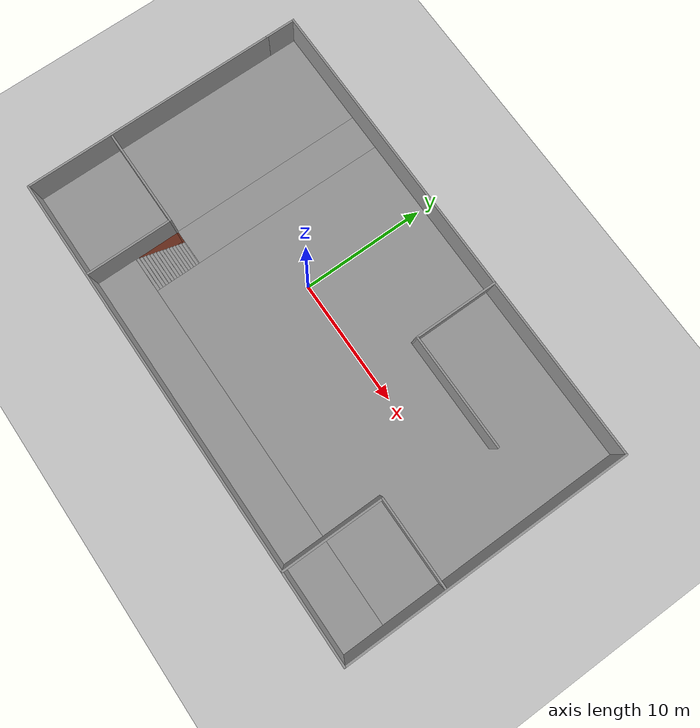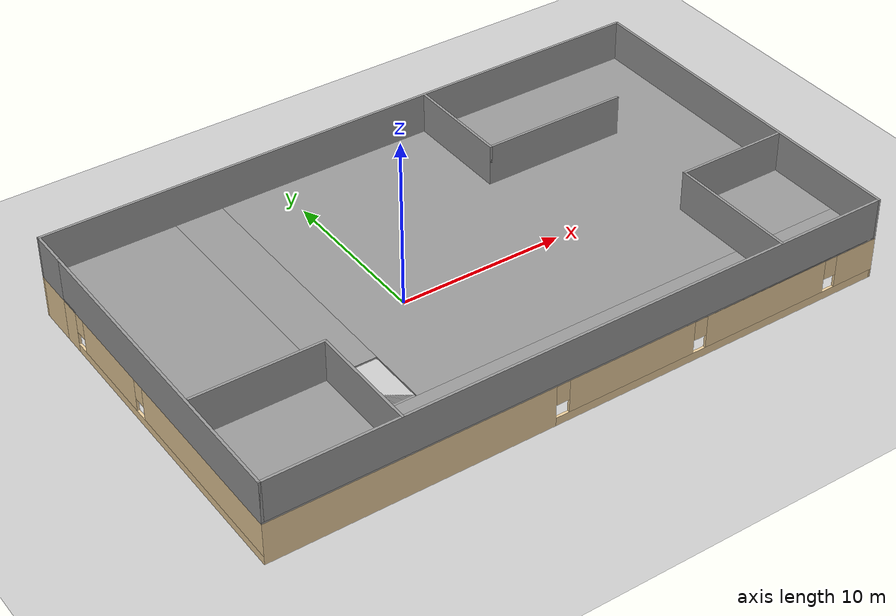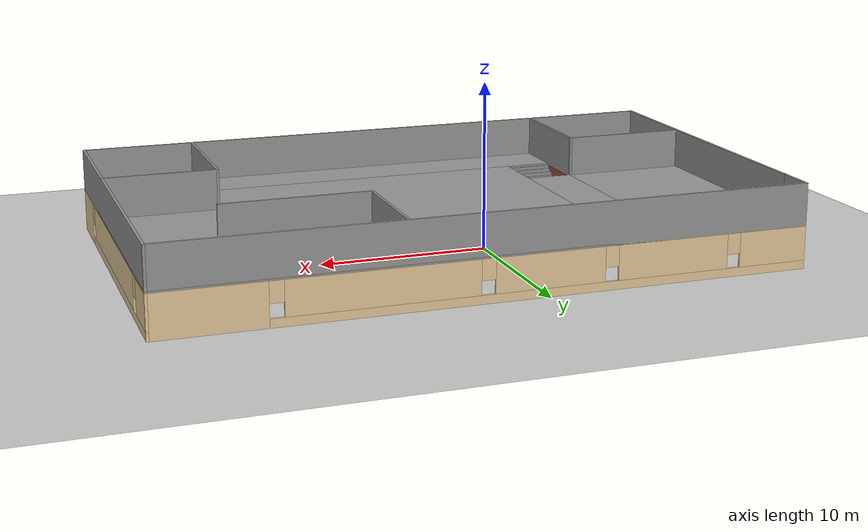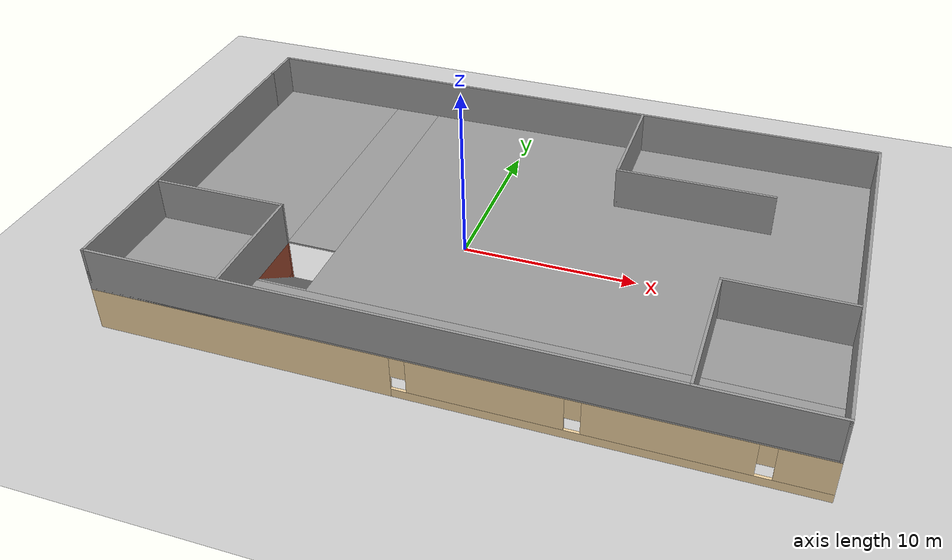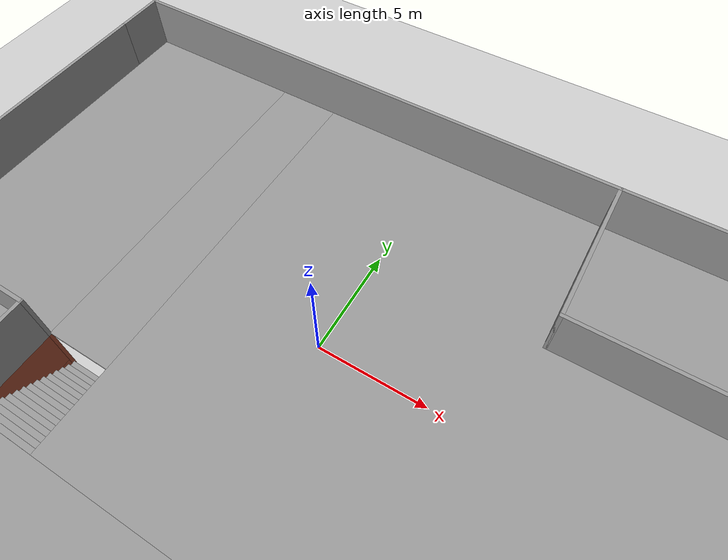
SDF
<sdf version="1.6">
 <world name="default">
  <light name="sun" type="directional">
   <pose>0 0 10 0 -0 0</pose>
   <diffuse>0.8 0.8 0.8 1</diffuse>
   <specular>0.1 0.1 0.1 1</specular>
   <attenuation>
    <range>1000</range>
    <constant>0.9</constant>
    <linear>0.01</linear>
    <quadratic>0.001</quadratic>
   </attenuation>
   <direction>-0.5 0.5 -1</direction>
  </light>
  <model name="ground_plane">
   <static>1</static>
   <link name="link">
    <collision name="collision">
     <geometry><plane><normal>0 0 1</normal><size>100 100</size></plane></geometry>
     <surface><friction><ode><mu>100</mu><mu2>50</mu2></ode></friction></surface>
    </collision>
    <visual name="visual">
     <cast_shadows>0</cast_shadows>
     <geometry><plane><normal>0 0 1</normal><size>100 100</size></plane></geometry>
     <material>
      <script><uri>file://media/materials/scripts/gazebo.material</uri><name>Gazebo/Grey</name></script>
     </material>
    </visual>
   </link>
  </model>
  <gravity>0 0 -9.8</gravity>
  <magnetic_field>6e-06 2.3e-05 -4.2e-05</magnetic_field>
  <atmosphere type="adiabatic"/>
  <physics name="default_physics" default="0" type="ode">
   <max_step_size>0.001</max_step_size>
   <real_time_factor>1</real_time_factor>
   <real_time_update_rate>1000</real_time_update_rate>
  </physics>
  <scene><ambient>0.4 0.4 0.4 1</ambient><background>0.7 0.7 0.7 1</background><shadows>1</shadows></scene>
  <spherical_coordinates>
   <surface_model>EARTH_WGS84</surface_model>
   <latitude_deg>0</latitude_deg>
   <longitude_deg>0</longitude_deg>
   <elevation>0</elevation>
   <heading_deg>0</heading_deg>
  </spherical_coordinates>
  <model name="storage">
   <pose>2.94649 -1.27432 0 0 -0 0</pose>
   <link name="Floor_0">
    <pose>0 0 2.5 0 -0 0</pose>
    <visual name="Floor_0_Visual_0">
     <pose>-14.7944 0 0.05 0 -0 0</pose>
     <geometry><box><size>7.66113 22 0.1</size></box></geometry>
     <material>
      <script><uri>file://media/materials/scripts/gazebo.material</uri><name>Gazebo/Grey</name></script>
      <ambient>1 1 1 1</ambient>
     </material>
    </visual>
    <collision name="Floor_0_Collision_0">
     <geometry><box><size>7.66113 22 0.1</size></box></geometry>
     <pose>-14.7944 0 0.05 0 -0 0</pose>
    </collision>
    <visual name="Floor_0_Visual_1">
     <pose>3.83056 -9.39198 0.05 0 -0 0</pose>
     <geometry><box><size>29.5889 3.21604 0.1</size></box></geometry>
     <material>
      <script><uri>file://media/materials/scripts/gazebo.material</uri><name>Gazebo/Grey</name></script>
      <ambient>1 1 1 1</ambient>
     </material>
    </visual>
    <collision name="Floor_0_Collision_1">
     <geometry><box><size>29.5889 3.21604 0.1</size></box></geometry>
     <pose>3.83056 -9.39198 0.05 0 -0 0</pose>
    </collision>
    <visual name="Floor_0_Visual_2">
     <pose>5.22762 1.60802 0.05 0 -0 0</pose>
     <geometry><box><size>26.7948 18.784 0.1</size></box></geometry>
     <material>
      <script><uri>file://media/materials/scripts/gazebo.material</uri><name>Gazebo/Grey</name></script>
      <ambient>1 1 1 1</ambient>
     </material>
    </visual>
    <collision name="Floor_0_Collision_2">
     <geometry><box><size>26.7948 18.784 0.1</size></box></geometry>
     <pose>5.22762 1.60802 0.05 0 -0 0</pose>
    </collision>
    <visual name="Floor_0_Visual_3">
     <pose>-9.56682 3.35802 0.05 0 -0 0</pose>
     <geometry><box><size>2.79412 15.284 0.1</size></box></geometry>
     <material>
      <script><uri>file://media/materials/scripts/gazebo.material</uri><name>Gazebo/Grey</name></script>
      <ambient>1 1 1 1</ambient>
     </material>
    </visual>
    <collision name="Floor_0_Collision_3">
     <geometry><box><size>2.79412 15.284 0.1</size></box></geometry>
     <pose>-9.56682 3.35802 0.05 0 -0 0</pose>
    </collision>
   </link>
   <link name="Stairs_0">
    <visual name="Stairs_0_Visual_0">
     <pose>-9.56682 -4.40063 0.083333 0 -0 0</pose>
     <geometry><box><size>2.79412 0.233333 0.166667</size></box></geometry>
     <material>
      <script><uri>file://media/materials/scripts/gazebo.material</uri><name>Gazebo/Grey</name></script>
      <ambient>0.419608 0.419608 0.419608 1</ambient>
     </material>
    </visual>
    <collision name="Stairs_0_Collision_0">
     <geometry><box><size>2.79412 0.233333 0.166667</size></box></geometry>
     <pose>-9.56682 -4.40063 0.083333 0 -0 0</pose>
    </collision>
    <visual name="Stairs_0_Visual_1">
     <pose>-9.56682 -4.63396 0.25 0 -0 0</pose>
     <geometry><box><size>2.79412 0.233333 0.166667</size></box></geometry>
     <material>
      <script><uri>file://media/materials/scripts/gazebo.material</uri><name>Gazebo/Grey</name></script>
      <ambient>0.419608 0.419608 0.419608 1</ambient>
     </material>
    </visual>
    <collision name="Stairs_0_Collision_1">
     <geometry><box><size>2.79412 0.233333 0.166667</size></box></geometry>
     <pose>-9.56682 -4.63396 0.25 0 -0 0</pose>
    </collision>
    <visual name="Stairs_0_Visual_2">
     <pose>-9.56682 -4.86729 0.416667 0 -0 0</pose>
     <geometry><box><size>2.79412 0.233333 0.166667</size></box></geometry>
     <material>
      <script><uri>file://media/materials/scripts/gazebo.material</uri><name>Gazebo/Grey</name></script>
      <ambient>0.419608 0.419608 0.419608 1</ambient>
     </material>
    </visual>
    <collision name="Stairs_0_Collision_2">
     <geometry><box><size>2.79412 0.233333 0.166667</size></box></geometry>
     <pose>-9.56682 -4.86729 0.416667 0 -0 0</pose>
    </collision>
    <visual name="Stairs_0_Visual_3">
     <pose>-9.56682 -5.10063 0.583333 0 -0 0</pose>
     <geometry><box><size>2.79412 0.233333 0.166667</size></box></geometry>
     <material>
      <script><uri>file://media/materials/scripts/gazebo.material</uri><name>Gazebo/Grey</name></script>
      <ambient>0.419608 0.419608 0.419608 1</ambient>
     </material>
    </visual>
    <collision name="Stairs_0_Collision_3">
     <geometry><box><size>2.79412 0.233333 0.166667</size></box></geometry>
     <pose>-9.56682 -5.10063 0.583333 0 -0 0</pose>
    </collision>
    <visual name="Stairs_0_Visual_4">
     <pose>-9.56682 -5.33396 0.75 0 -0 0</pose>
     <geometry><box><size>2.79412 0.233333 0.166667</size></box></geometry>
     <material>
      <script><uri>file://media/materials/scripts/gazebo.material</uri><name>Gazebo/Grey</name></script>
      <ambient>0.419608 0.419608 0.419608 1</ambient>
     </material>
    </visual>
    <collision name="Stairs_0_Collision_4">
     <geometry><box><size>2.79412 0.233333 0.166667</size></box></geometry>
     <pose>-9.56682 -5.33396 0.75 0 -0 0</pose>
    </collision>
    <visual name="Stairs_0_Visual_5">
     <pose>-9.56682 -5.56729 0.916667 0 -0 0</pose>
     <geometry><box><size>2.79412 0.233333 0.166667</size></box></geometry>
     <material>
      <script><uri>file://media/materials/scripts/gazebo.material</uri><name>Gazebo/Grey</name></script>
      <ambient>0.419608 0.419608 0.419608 1</ambient>
     </material>
    </visual>
    <collision name="Stairs_0_Collision_5">
     <geometry><box><size>2.79412 0.233333 0.166667</size></box></geometry>
     <pose>-9.56682 -5.56729 0.916667 0 -0 0</pose>
    </collision>
    <visual name="Stairs_0_Visual_6">
     <pose>-9.56682 -5.80063 1.08333 0 -0 0</pose>
     <geometry><box><size>2.79412 0.233333 0.166667</size></box></geometry>
     <material>
      <script><uri>file://media/materials/scripts/gazebo.material</uri><name>Gazebo/Grey</name></script>
      <ambient>0.419608 0.419608 0.419608 1</ambient>
     </material>
    </visual>
    <collision name="Stairs_0_Collision_6">
     <geometry><box><size>2.79412 0.233333 0.166667</size></box></geometry>
     <pose>-9.56682 -5.80063 1.08333 0 -0 0</pose>
    </collision>
    <visual name="Stairs_0_Visual_7">
     <pose>-9.56682 -6.03396 1.25 0 -0 0</pose>
     <geometry><box><size>2.79412 0.233333 0.166667</size></box></geometry>
     <material>
      <script><uri>file://media/materials/scripts/gazebo.material</uri><name>Gazebo/Grey</name></script>
      <ambient>0.419608 0.419608 0.419608 1</ambient>
     </material>
    </visual>
    <collision name="Stairs_0_Collision_7">
     <geometry><box><size>2.79412 0.233333 0.166667</size></box></geometry>
     <pose>-9.56682 -6.03396 1.25 0 -0 0</pose>
    </collision>
    <visual name="Stairs_0_Visual_8">
     <pose>-9.56682 -6.26729 1.41667 0 -0 0</pose>
     <geometry><box><size>2.79412 0.233333 0.166667</size></box></geometry>
     <material>
      <script><uri>file://media/materials/scripts/gazebo.material</uri><name>Gazebo/Grey</name></script>
      <ambient>0.419608 0.419608 0.419608 1</ambient>
     </material>
    </visual>
    <collision name="Stairs_0_Collision_8">
     <geometry><box><size>2.79412 0.233333 0.166667</size></box></geometry>
     <pose>-9.56682 -6.26729 1.41667 0 -0 0</pose>
    </collision>
    <visual name="Stairs_0_Visual_9">
     <pose>-9.56682 -6.50063 1.58333 0 -0 0</pose>
     <geometry><box><size>2.79412 0.233333 0.166667</size></box></geometry>
     <material>
      <script><uri>file://media/materials/scripts/gazebo.material</uri><name>Gazebo/Grey</name></script>
      <ambient>0.419608 0.419608 0.419608 1</ambient>
     </material>
    </visual>
    <collision name="Stairs_0_Collision_9">
     <geometry><box><size>2.79412 0.233333 0.166667</size></box></geometry>
     <pose>-9.56682 -6.50063 1.58333 0 -0 0</pose>
    </collision>
    <visual name="Stairs_0_Visual_10">
     <pose>-9.56682 -6.73396 1.75 0 -0 0</pose>
     <geometry><box><size>2.79412 0.233333 0.166667</size></box></geometry>
     <material>
      <script><uri>file://media/materials/scripts/gazebo.material</uri><name>Gazebo/Grey</name></script>
      <ambient>0.419608 0.419608 0.419608 1</ambient>
     </material>
    </visual>
    <collision name="Stairs_0_Collision_10">
     <geometry><box><size>2.79412 0.233333 0.166667</size></box></geometry>
     <pose>-9.56682 -6.73396 1.75 0 -0 0</pose>
    </collision>
    <visual name="Stairs_0_Visual_11">
     <pose>-9.56682 -6.9673 1.91667 0 -0 0</pose>
     <geometry><box><size>2.79412 0.233333 0.166667</size></box></geometry>
     <material>
      <script><uri>file://media/materials/scripts/gazebo.material</uri><name>Gazebo/Grey</name></script>
      <ambient>0.419608 0.419608 0.419608 1</ambient>
     </material>
    </visual>
    <collision name="Stairs_0_Collision_11">
     <geometry><box><size>2.79412 0.233333 0.166667</size></box></geometry>
     <pose>-9.56682 -6.9673 1.91667 0 -0 0</pose>
    </collision>
    <visual name="Stairs_0_Visual_12">
     <pose>-9.56682 -7.20063 2.08333 0 -0 0</pose>
     <geometry><box><size>2.79412 0.233333 0.166667</size></box></geometry>
     <material>
      <script><uri>file://media/materials/scripts/gazebo.material</uri><name>Gazebo/Grey</name></script>
      <ambient>0.419608 0.419608 0.419608 1</ambient>
     </material>
    </visual>
    <collision name="Stairs_0_Collision_12">
     <geometry><box><size>2.79412 0.233333 0.166667</size></box></geometry>
     <pose>-9.56682 -7.20063 2.08333 0 -0 0</pose>
    </collision>
    <visual name="Stairs_0_Visual_13">
     <pose>-9.56682 -7.43396 2.25 0 -0 0</pose>
     <geometry><box><size>2.79412 0.233333 0.166667</size></box></geometry>
     <material>
      <script><uri>file://media/materials/scripts/gazebo.material</uri><name>Gazebo/Grey</name></script>
      <ambient>0.419608 0.419608 0.419608 1</ambient>
     </material>
    </visual>
    <collision name="Stairs_0_Collision_13">
     <geometry><box><size>2.79412 0.233333 0.166667</size></box></geometry>
     <pose>-9.56682 -7.43396 2.25 0 -0 0</pose>
    </collision>
    <visual name="Stairs_0_Visual_14">
     <pose>-9.56682 -7.6673 2.41667 0 -0 0</pose>
     <geometry><box><size>2.79412 0.233333 0.166667</size></box></geometry>
     <material>
      <script><uri>file://media/materials/scripts/gazebo.material</uri><name>Gazebo/Grey</name></script>
      <ambient>0.419608 0.419608 0.419608 1</ambient>
     </material>
    </visual>
    <collision name="Stairs_0_Collision_14">
     <geometry><box><size>2.79412 0.233333 0.166667</size></box></geometry>
     <pose>-9.56682 -7.6673 2.41667 0 -0 0</pose>
    </collision>
   </link>
   <link name="Wall_1">
    <pose>-18.55 -1.125 0 0 0 -1.5708</pose>
    <visual name="Wall_1_Visual_0">
     <pose>-9.16747 0 1.25 0 -0 0</pose>
     <geometry><box><size>1.41505 0.15 2.5</size></box></geometry>
     <material>
      <script><uri>file://media/materials/scripts/gazebo.material</uri><name>Gazebo/Grey</name></script>
      <ambient>0.921569 0.807843 0.615686 1</ambient>
     </material>
    </visual>
    <collision name="Wall_1_Collision_0">
     <geometry><box><size>1.41505 0.15 2.5</size></box></geometry>
     <pose>-9.16747 0 1.25 0 -0 0</pose>
    </collision>
    <visual name="Wall_1_Visual_1">
     <pose>0.707526 0 0.25 0 -0 0</pose>
     <geometry><box><size>18.3349 0.15 0.5</size></box></geometry>
     <material>
      <script><uri>file://media/materials/scripts/gazebo.material</uri><name>Gazebo/Grey</name></script>
      <ambient>0.921569 0.807843 0.615686 1</ambient>
     </material>
    </visual>
    <collision name="Wall_1_Collision_1">
     <geometry><box><size>18.3349 0.15 0.5</size></box></geometry>
     <pose>0.707526 0 0.25 0 -0 0</pose>
    </collision>
    <visual name="Wall_1_Visual_2">
     <pose>-4.94285 0 1.5 0 -0 0</pose>
     <geometry><box><size>5.43421 0.15 2</size></box></geometry>
     <material>
      <script><uri>file://media/materials/scripts/gazebo.material</uri><name>Gazebo/Grey</name></script>
      <ambient>0.921569 0.807843 0.615686 1</ambient>
     </material>
    </visual>
    <collision name="Wall_1_Collision_2">
     <geometry><box><size>5.43421 0.15 2</size></box></geometry>
     <pose>-4.94285 0 1.5 0 -0 0</pose>
    </collision>
    <visual name="Wall_1_Visual_3">
     <pose>4.22463 0 1.5 0 -0 0</pose>
     <geometry><box><size>11.3007 0.15 2</size></box></geometry>
     <material>
      <script><uri>file://media/materials/scripts/gazebo.material</uri><name>Gazebo/Grey</name></script>
      <ambient>0.921569 0.807843 0.615686 1</ambient>
     </material>
    </visual>
    <collision name="Wall_1_Collision_3">
     <geometry><box><size>11.3007 0.15 2</size></box></geometry>
     <pose>4.22463 0 1.5 0 -0 0</pose>
    </collision>
    <visual name="Wall_1_Visual_4">
     <pose>-8.05995 0 1.9 0 -0 0</pose>
     <geometry><box><size>0.8 0.15 1.2</size></box></geometry>
     <material>
      <script><uri>file://media/materials/scripts/gazebo.material</uri><name>Gazebo/Grey</name></script>
      <ambient>0.921569 0.807843 0.615686 1</ambient>
     </material>
    </visual>
    <collision name="Wall_1_Collision_4">
     <geometry><box><size>0.8 0.15 1.2</size></box></geometry>
     <pose>-8.05995 0 1.9 0 -0 0</pose>
    </collision>
    <visual name="Wall_1_Visual_5">
     <pose>-1.82574 0 1.9 0 -0 0</pose>
     <geometry><box><size>0.8 0.15 1.2</size></box></geometry>
     <material>
      <script><uri>file://media/materials/scripts/gazebo.material</uri><name>Gazebo/Grey</name></script>
      <ambient>0.921569 0.807843 0.615686 1</ambient>
     </material>
    </visual>
    <collision name="Wall_1_Collision_5">
     <geometry><box><size>0.8 0.15 1.2</size></box></geometry>
     <pose>-1.82574 0 1.9 0 -0 0</pose>
    </collision>
   </link>
   <link name="Wall_10">
    <pose>-11.0196 -7.61598 0 0 -0 1.5708</pose>
    <visual name="Wall_10_Visual_0">
     <pose>-2.69712 0 1.25 0 -0 0</pose>
     <geometry><box><size>1.35576 0.15 2.5</size></box></geometry>
     <material>
      <script><uri>file://media/materials/scripts/gazebo.material</uri><name>Gazebo/Bricks</name></script>
      <ambient>1 1 1 1</ambient>
     </material>
    </visual>
    <collision name="Wall_10_Collision_0">
     <geometry><box><size>1.35576 0.15 2.5</size></box></geometry>
     <pose>-2.69712 0 1.25 0 -0 0</pose>
    </collision>
    <visual name="Wall_10_Visual_1">
     <pose>0.677878 0 0.25 0 -0 0</pose>
     <geometry><box><size>5.39424 0.15 0.5</size></box></geometry>
     <material>
      <script><uri>file://media/materials/scripts/gazebo.material</uri><name>Gazebo/Bricks</name></script>
      <ambient>1 1 1 1</ambient>
     </material>
    </visual>
    <collision name="Wall_10_Collision_1">
     <geometry><box><size>5.39424 0.15 0.5</size></box></geometry>
     <pose>0.677878 0 0.25 0 -0 0</pose>
    </collision>
    <visual name="Wall_10_Visual_2">
     <pose>1.07788 0 1.5 0 -0 0</pose>
     <geometry><box><size>4.59424 0.15 2</size></box></geometry>
     <material>
      <script><uri>file://media/materials/scripts/gazebo.material</uri><name>Gazebo/Bricks</name></script>
      <ambient>1 1 1 1</ambient>
     </material>
    </visual>
    <collision name="Wall_10_Collision_2">
     <geometry><box><size>4.59424 0.15 2</size></box></geometry>
     <pose>1.07788 0 1.5 0 -0 0</pose>
    </collision>
    <visual name="Wall_10_Visual_3">
     <pose>-1.61925 0 1.9 0 -0 0</pose>
     <geometry><box><size>0.8 0.15 1.2</size></box></geometry>
     <material>
      <script><uri>file://media/materials/scripts/gazebo.material</uri><name>Gazebo/Bricks</name></script>
      <ambient>1 1 1 1</ambient>
     </material>
    </visual>
    <collision name="Wall_10_Collision_3">
     <geometry><box><size>0.8 0.15 1.2</size></box></geometry>
     <pose>-1.61925 0 1.9 0 -0 0</pose>
    </collision>
   </link>
   <link name="Wall_11">
    <pose>-14.6946 -4.31598 0 0 -0 3.14159</pose>
    <visual name="Wall_11_Visual_0">
     <pose>-2.69663 0 1.25 0 -0 0</pose>
     <geometry><box><size>2.10674 0.15 2.5</size></box></geometry>
     <material>
      <script><uri>file://media/materials/scripts/gazebo.material</uri><name>Gazebo/Bricks</name></script>
      <ambient>1 1 1 1</ambient>
     </material>
    </visual>
    <collision name="Wall_11_Collision_0">
     <geometry><box><size>2.10674 0.15 2.5</size></box></geometry>
     <pose>-2.69663 0 1.25 0 -0 0</pose>
    </collision>
    <visual name="Wall_11_Visual_1">
     <pose>0.21527 0 1.25 0 -0 0</pose>
     <geometry><box><size>1.91706 0.15 2.5</size></box></geometry>
     <material>
      <script><uri>file://media/materials/scripts/gazebo.material</uri><name>Gazebo/Bricks</name></script>
      <ambient>1 1 1 1</ambient>
     </material>
    </visual>
    <collision name="Wall_11_Collision_1">
     <geometry><box><size>1.91706 0.15 2.5</size></box></geometry>
     <pose>0.21527 0 1.25 0 -0 0</pose>
    </collision>
    <visual name="Wall_11_Visual_2">
     <pose>2.4619 0 0.25 0 -0 0</pose>
     <geometry><box><size>2.5762 0.15 0.5</size></box></geometry>
     <material>
      <script><uri>file://media/materials/scripts/gazebo.material</uri><name>Gazebo/Bricks</name></script>
      <ambient>1 1 1 1</ambient>
     </material>
    </visual>
    <collision name="Wall_11_Collision_2">
     <geometry><box><size>2.5762 0.15 0.5</size></box></geometry>
     <pose>2.4619 0 0.25 0 -0 0</pose>
    </collision>
    <visual name="Wall_11_Visual_3">
     <pose>2.8619 0 1.5 0 -0 0</pose>
     <geometry><box><size>1.7762 0.15 2</size></box></geometry>
     <material>
      <script><uri>file://media/materials/scripts/gazebo.material</uri><name>Gazebo/Bricks</name></script>
      <ambient>1 1 1 1</ambient>
     </material>
    </visual>
    <collision name="Wall_11_Collision_3">
     <geometry><box><size>1.7762 0.15 2</size></box></geometry>
     <pose>2.8619 0 1.5 0 -0 0</pose>
    </collision>
    <visual name="Wall_11_Visual_4">
     <pose>1.5738 0 1.9 0 -0 0</pose>
     <geometry><box><size>0.8 0.15 1.2</size></box></geometry>
     <material>
      <script><uri>file://media/materials/scripts/gazebo.material</uri><name>Gazebo/Bricks</name></script>
      <ambient>1 1 1 1</ambient>
     </material>
    </visual>
    <collision name="Wall_11_Collision_4">
     <geometry><box><size>0.8 0.15 1.2</size></box></geometry>
     <pose>1.5738 0 1.9 0 -0 0</pose>
    </collision>
    <visual name="Wall_11_Visual_5">
     <pose>-1.19326 0 2.25 0 -0 0</pose>
     <geometry><box><size>0.9 0.15 0.5</size></box></geometry>
     <material>
      <script><uri>file://media/materials/scripts/gazebo.material</uri><name>Gazebo/Bricks</name></script>
      <ambient>1 1 1 1</ambient>
     </material>
    </visual>
    <collision name="Wall_11_Collision_5">
     <geometry><box><size>0.9 0.15 0.5</size></box></geometry>
     <pose>-1.19326 0 2.25 0 -0 0</pose>
    </collision>
   </link>
   <link name="Wall_13">
    <pose>11.9007 -7.08371 0 0 -0 1.5708</pose>
    <visual name="Wall_13_Visual_0">
     <pose>-2.86147 0 1.25 0 -0 0</pose>
     <geometry><box><size>2.02706 0.15 2.5</size></box></geometry>
     <material>
      <script><uri>file://media/materials/scripts/gazebo.material</uri><name>Gazebo/Bricks</name></script>
      <ambient>1 1 1 1</ambient>
     </material>
    </visual>
    <collision name="Wall_13_Collision_0">
     <geometry><box><size>2.02706 0.15 2.5</size></box></geometry>
     <pose>-2.86147 0 1.25 0 -0 0</pose>
    </collision>
    <visual name="Wall_13_Visual_1">
     <pose>2.79805 0 1.25 0 -0 0</pose>
     <geometry><box><size>2.15389 0.15 2.5</size></box></geometry>
     <material>
      <script><uri>file://media/materials/scripts/gazebo.material</uri><name>Gazebo/Bricks</name></script>
      <ambient>1 1 1 1</ambient>
     </material>
    </visual>
    <collision name="Wall_13_Collision_1">
     <geometry><box><size>2.15389 0.15 2.5</size></box></geometry>
     <pose>2.79805 0 1.25 0 -0 0</pose>
    </collision>
    <visual name="Wall_13_Visual_2">
     <pose>-0.513417 0 0.25 0 -0 0</pose>
     <geometry><box><size>2.66905 0.15 0.5</size></box></geometry>
     <material>
      <script><uri>file://media/materials/scripts/gazebo.material</uri><name>Gazebo/Bricks</name></script>
      <ambient>1 1 1 1</ambient>
     </material>
    </visual>
    <collision name="Wall_13_Collision_2">
     <geometry><box><size>2.66905 0.15 0.5</size></box></geometry>
     <pose>-0.513417 0 0.25 0 -0 0</pose>
    </collision>
    <visual name="Wall_13_Visual_3">
     <pose>-0.113417 0 1.5 0 -0 0</pose>
     <geometry><box><size>1.86905 0.15 2</size></box></geometry>
     <material>
      <script><uri>file://media/materials/scripts/gazebo.material</uri><name>Gazebo/Bricks</name></script>
      <ambient>1 1 1 1</ambient>
     </material>
    </visual>
    <collision name="Wall_13_Collision_3">
     <geometry><box><size>1.86905 0.15 2</size></box></geometry>
     <pose>-0.113417 0 1.5 0 -0 0</pose>
    </collision>
    <visual name="Wall_13_Visual_4">
     <pose>-1.44794 0 1.9 0 -0 0</pose>
     <geometry><box><size>0.8 0.15 1.2</size></box></geometry>
     <material>
      <script><uri>file://media/materials/scripts/gazebo.material</uri><name>Gazebo/Bricks</name></script>
      <ambient>1 1 1 1</ambient>
     </material>
    </visual>
    <collision name="Wall_13_Collision_4">
     <geometry><box><size>0.8 0.15 1.2</size></box></geometry>
     <pose>-1.44794 0 1.9 0 -0 0</pose>
    </collision>
    <visual name="Wall_13_Visual_5">
     <pose>1.27111 0 2.25 0 -0 0</pose>
     <geometry><box><size>0.9 0.15 0.5</size></box></geometry>
     <material>
      <script><uri>file://media/materials/scripts/gazebo.material</uri><name>Gazebo/Bricks</name></script>
      <ambient>1 1 1 1</ambient>
     </material>
    </visual>
    <collision name="Wall_13_Collision_5">
     <geometry><box><size>0.9 0.15 0.5</size></box></geometry>
     <pose>1.27111 0 2.25 0 -0 0</pose>
    </collision>
   </link>
   <link name="Wall_14">
    <pose>15.2007 -3.28371 0 0 -0 0</pose>
    <visual name="Wall_14_Visual_0">
     <pose>-1.68608 0 1.25 0 -0 0</pose>
     <geometry><box><size>3.37785 0.15 2.5</size></box></geometry>
     <material>
      <script><uri>file://media/materials/scripts/gazebo.material</uri><name>Gazebo/Bricks</name></script>
      <ambient>1 1 1 1</ambient>
     </material>
    </visual>
    <collision name="Wall_14_Collision_0">
     <geometry><box><size>3.37785 0.15 2.5</size></box></geometry>
     <pose>-1.68608 0 1.25 0 -0 0</pose>
    </collision>
    <visual name="Wall_14_Visual_1">
     <pose>1.68892 0 0.25 0 -0 0</pose>
     <geometry><box><size>3.37215 0.15 0.5</size></box></geometry>
     <material>
      <script><uri>file://media/materials/scripts/gazebo.material</uri><name>Gazebo/Bricks</name></script>
      <ambient>1 1 1 1</ambient>
     </material>
    </visual>
    <collision name="Wall_14_Collision_1">
     <geometry><box><size>3.37215 0.15 0.5</size></box></geometry>
     <pose>1.68892 0 0.25 0 -0 0</pose>
    </collision>
    <visual name="Wall_14_Visual_2">
     <pose>2.08892 0 1.5 0 -0 0</pose>
     <geometry><box><size>2.57215 0.15 2</size></box></geometry>
     <material>
      <script><uri>file://media/materials/scripts/gazebo.material</uri><name>Gazebo/Bricks</name></script>
      <ambient>1 1 1 1</ambient>
     </material>
    </visual>
    <collision name="Wall_14_Collision_2">
     <geometry><box><size>2.57215 0.15 2</size></box></geometry>
     <pose>2.08892 0 1.5 0 -0 0</pose>
    </collision>
    <visual name="Wall_14_Visual_3">
     <pose>0.402845 0 1.9 0 -0 0</pose>
     <geometry><box><size>0.8 0.15 1.2</size></box></geometry>
     <material>
      <script><uri>file://media/materials/scripts/gazebo.material</uri><name>Gazebo/Bricks</name></script>
      <ambient>1 1 1 1</ambient>
     </material>
    </visual>
    <collision name="Wall_14_Collision_3">
     <geometry><box><size>0.8 0.15 1.2</size></box></geometry>
     <pose>0.402845 0 1.9 0 -0 0</pose>
    </collision>
   </link>
   <link name="Wall_16">
    <collision name="Wall_16_Collision">
     <geometry><box><size>19.75 0.15 2.5</size></box></geometry>
     <pose>0 0 1.25 0 -0 0</pose>
    </collision>
    <visual name="Wall_16_Visual">
     <pose>0 0 1.25 0 -0 0</pose>
     <geometry><box><size>19.75 0.15 2.5</size></box></geometry>
     <material>
      <script><uri>file://media/materials/scripts/gazebo.material</uri><name>Gazebo/Grey</name></script>
      <ambient>1 1 1 1</ambient>
     </material>
    </visual>
    <pose>-18.55 -1.125 2.5 0 0 -1.5708</pose>
   </link>
   <link name="Wall_17">
    <collision name="Wall_17_Collision">
     <geometry><box><size>37.25 0.15 2.5</size></box></geometry>
     <pose>0 0 1.25 0 -0 0</pose>
    </collision>
    <visual name="Wall_17_Visual">
     <pose>0 0 1.25 0 -0 0</pose>
     <geometry><box><size>37.25 0.15 2.5</size></box></geometry>
     <material>
      <script><uri>file://media/materials/scripts/gazebo.material</uri><name>Gazebo/Grey</name></script>
      <ambient>1 1 1 1</ambient>
     </material>
    </visual>
    <pose>0 -10.925 2.5 0 -0 0</pose>
   </link>
   <link name="Wall_18">
    <collision name="Wall_18_Collision">
     <geometry><box><size>22 0.15 2.5</size></box></geometry>
     <pose>0 0 1.25 0 -0 0</pose>
    </collision>
    <visual name="Wall_18_Visual">
     <pose>0 0 1.25 0 -0 0</pose>
     <geometry><box><size>22 0.15 2.5</size></box></geometry>
     <material>
      <script><uri>file://media/materials/scripts/gazebo.material</uri><name>Gazebo/Grey</name></script>
      <ambient>1 1 1 1</ambient>
     </material>
    </visual>
    <pose>18.55 0 2.5 0 -0 1.5708</pose>
   </link>
   <link name="Wall_19">
    <collision name="Wall_19_Collision">
     <geometry><box><size>37.25 0.15 2.5</size></box></geometry>
     <pose>0 0 1.25 0 -0 0</pose>
    </collision>
    <visual name="Wall_19_Visual">
     <pose>0 0 1.25 0 -0 0</pose>
     <geometry><box><size>37.25 0.15 2.5</size></box></geometry>
     <material>
      <script><uri>file://media/materials/scripts/gazebo.material</uri><name>Gazebo/Grey</name></script>
      <ambient>1 1 1 1</ambient>
     </material>
    </visual>
    <pose>0 10.925 2.5 0 -0 3.14159</pose>
   </link>
   <link name="Wall_2">
    <pose>0 -10.925 0 0 -0 0</pose>
    <visual name="Wall_2_Visual_0">
     <pose>-10.4329 0 1.25 0 -0 0</pose>
     <geometry><box><size>16.3841 0.15 2.5</size></box></geometry>
     <material>
      <script><uri>file://media/materials/scripts/gazebo.material</uri><name>Gazebo/Grey</name></script>
      <ambient>0.921569 0.807843 0.615686 1</ambient>
     </material>
    </visual>
    <collision name="Wall_2_Collision_0">
     <geometry><box><size>16.3841 0.15 2.5</size></box></geometry>
     <pose>-10.4329 0 1.25 0 -0 0</pose>
    </collision>
    <visual name="Wall_2_Visual_1">
     <pose>8.19207 0 0.25 0 -0 0</pose>
     <geometry><box><size>20.8659 0.15 0.5</size></box></geometry>
     <material>
      <script><uri>file://media/materials/scripts/gazebo.material</uri><name>Gazebo/Grey</name></script>
      <ambient>0.921569 0.807843 0.615686 1</ambient>
     </material>
    </visual>
    <collision name="Wall_2_Collision_1">
     <geometry><box><size>20.8659 0.15 0.5</size></box></geometry>
     <pose>8.19207 0 0.25 0 -0 0</pose>
    </collision>
    <visual name="Wall_2_Visual_2">
     <pose>2.46838 0 1.5 0 -0 0</pose>
     <geometry><box><size>7.81846 0.15 2</size></box></geometry>
     <material>
      <script><uri>file://media/materials/scripts/gazebo.material</uri><name>Gazebo/Grey</name></script>
      <ambient>0.921569 0.807843 0.615686 1</ambient>
     </material>
    </visual>
    <collision name="Wall_2_Collision_2">
     <geometry><box><size>7.81846 0.15 2</size></box></geometry>
     <pose>2.46838 0 1.5 0 -0 0</pose>
    </collision>
    <visual name="Wall_2_Visual_3">
     <pose>11.1533 0 1.5 0 -0 0</pose>
     <geometry><box><size>7.95147 0.15 2</size></box></geometry>
     <material>
      <script><uri>file://media/materials/scripts/gazebo.material</uri><name>Gazebo/Grey</name></script>
      <ambient>0.921569 0.807843 0.615686 1</ambient>
     </material>
    </visual>
    <collision name="Wall_2_Collision_3">
     <geometry><box><size>7.95147 0.15 2</size></box></geometry>
     <pose>11.1533 0 1.5 0 -0 0</pose>
    </collision>
    <visual name="Wall_2_Visual_4">
     <pose>17.277 0 1.5 0 -0 0</pose>
     <geometry><box><size>2.69592 0.15 2</size></box></geometry>
     <material>
      <script><uri>file://media/materials/scripts/gazebo.material</uri><name>Gazebo/Grey</name></script>
      <ambient>0.921569 0.807843 0.615686 1</ambient>
     </material>
    </visual>
    <collision name="Wall_2_Collision_4">
     <geometry><box><size>2.69592 0.15 2</size></box></geometry>
     <pose>17.277 0 1.5 0 -0 0</pose>
    </collision>
    <visual name="Wall_2_Visual_5">
     <pose>-1.84085 0 1.9 0 -0 0</pose>
     <geometry><box><size>0.8 0.15 1.2</size></box></geometry>
     <material>
      <script><uri>file://media/materials/scripts/gazebo.material</uri><name>Gazebo/Grey</name></script>
      <ambient>0.921569 0.807843 0.615686 1</ambient>
     </material>
    </visual>
    <collision name="Wall_2_Collision_5">
     <geometry><box><size>0.8 0.15 1.2</size></box></geometry>
     <pose>-1.84085 0 1.9 0 -0 0</pose>
    </collision>
    <visual name="Wall_2_Visual_6">
     <pose>6.77761 0 1.9 0 -0 0</pose>
     <geometry><box><size>0.8 0.15 1.2</size></box></geometry>
     <material>
      <script><uri>file://media/materials/scripts/gazebo.material</uri><name>Gazebo/Grey</name></script>
      <ambient>0.921569 0.807843 0.615686 1</ambient>
     </material>
    </visual>
    <collision name="Wall_2_Collision_6">
     <geometry><box><size>0.8 0.15 1.2</size></box></geometry>
     <pose>6.77761 0 1.9 0 -0 0</pose>
    </collision>
    <visual name="Wall_2_Visual_7">
     <pose>15.5291 0 1.9 0 -0 0</pose>
     <geometry><box><size>0.8 0.15 1.2</size></box></geometry>
     <material>
      <script><uri>file://media/materials/scripts/gazebo.material</uri><name>Gazebo/Grey</name></script>
      <ambient>0.921569 0.807843 0.615686 1</ambient>
     </material>
    </visual>
    <collision name="Wall_2_Collision_7">
     <geometry><box><size>0.8 0.15 1.2</size></box></geometry>
     <pose>15.5291 0 1.9 0 -0 0</pose>
    </collision>
   </link>
   <link name="Wall_20">
    <collision name="Wall_20_Collision">
     <geometry><box><size>2.4 0.15 2.5</size></box></geometry>
     <pose>0 0 1.25 0 -0 0</pose>
    </collision>
    <visual name="Wall_20_Visual">
     <pose>0 0 1.25 0 -0 0</pose>
     <geometry><box><size>2.4 0.15 2.5</size></box></geometry>
     <material>
      <script><uri>file://media/materials/scripts/gazebo.material</uri><name>Gazebo/Grey</name></script>
      <ambient>1 1 1 1</ambient>
     </material>
    </visual>
    <pose>-18.55 9.8 2.5 0 0 -1.5708</pose>
   </link>
   <link name="Wall_21">
    <collision name="Wall_21_Collision">
     <geometry><box><size>6.5 0.15 2.5</size></box></geometry>
     <pose>0 0 1.25 0 -0 0</pose>
    </collision>
    <visual name="Wall_21_Visual">
     <pose>0 0 1.25 0 -0 0</pose>
     <geometry><box><size>6.5 0.15 2.5</size></box></geometry>
     <material>
      <script><uri>file://media/materials/scripts/gazebo.material</uri><name>Gazebo/Grey</name></script>
      <ambient>1 1 1 1</ambient>
     </material>
    </visual>
    <pose>4.92417 7.73804 2.5 0 0 -1.5708</pose>
   </link>
   <link name="Wall_22">
    <collision name="Wall_22_Collision">
     <geometry><box><size>8.75 0.15 2.5</size></box></geometry>
     <pose>0 0 1.25 0 -0 0</pose>
    </collision>
    <visual name="Wall_22_Visual">
     <pose>0 0 1.25 0 -0 0</pose>
     <geometry><box><size>8.75 0.15 2.5</size></box></geometry>
     <material>
      <script><uri>file://media/materials/scripts/gazebo.material</uri><name>Gazebo/Grey</name></script>
      <ambient>1 1 1 1</ambient>
     </material>
    </visual>
    <pose>9.22417 4.56304 2.5 0 -0 0</pose>
   </link>
   <link name="Wall_23">
    <collision name="Wall_23_Collision">
     <geometry><box><size>6.75 0.15 2.5</size></box></geometry>
     <pose>0 0 1.25 0 -0 0</pose>
    </collision>
    <visual name="Wall_23_Visual">
     <pose>0 0 1.25 0 -0 0</pose>
     <geometry><box><size>6.75 0.15 2.5</size></box></geometry>
     <material>
      <script><uri>file://media/materials/scripts/gazebo.material</uri><name>Gazebo/Grey</name></script>
      <ambient>1 1 1 1</ambient>
     </material>
    </visual>
    <pose>-11.0196 -7.61598 2.5 0 -0 1.5708</pose>
   </link>
   <link name="Wall_24">
    <collision name="Wall_24_Collision">
     <geometry><box><size>7.5 0.15 2.5</size></box></geometry>
     <pose>0 0 1.25 0 -0 0</pose>
    </collision>
    <visual name="Wall_24_Visual">
     <pose>0 0 1.25 0 -0 0</pose>
     <geometry><box><size>7.5 0.15 2.5</size></box></geometry>
     <material>
      <script><uri>file://media/materials/scripts/gazebo.material</uri><name>Gazebo/Grey</name></script>
      <ambient>1 1 1 1</ambient>
     </material>
    </visual>
    <pose>-14.6946 -4.31598 2.5 0 -0 3.14159</pose>
   </link>
   <link name="Wall_25">
    <collision name="Wall_25_Collision">
     <geometry><box><size>7.75 0.15 2.5</size></box></geometry>
     <pose>0 0 1.25 0 -0 0</pose>
    </collision>
    <visual name="Wall_25_Visual">
     <pose>0 0 1.25 0 -0 0</pose>
     <geometry><box><size>7.75 0.15 2.5</size></box></geometry>
     <material>
      <script><uri>file://media/materials/scripts/gazebo.material</uri><name>Gazebo/Grey</name></script>
      <ambient>1 1 1 1</ambient>
     </material>
    </visual>
    <pose>11.9007 -7.08371 2.5 0 -0 1.5708</pose>
   </link>
   <link name="Wall_26">
    <collision name="Wall_26_Collision">
     <geometry><box><size>6.75 0.15 2.5</size></box></geometry>
     <pose>0 0 1.25 0 -0 0</pose>
    </collision>
    <visual name="Wall_26_Visual">
     <pose>0 0 1.25 0 -0 0</pose>
     <geometry><box><size>6.75 0.15 2.5</size></box></geometry>
     <material>
      <script><uri>file://media/materials/scripts/gazebo.material</uri><name>Gazebo/Grey</name></script>
      <ambient>1 1 1 1</ambient>
     </material>
    </visual>
    <pose>15.2007 -3.28371 2.5 0 -0 0</pose>
   </link>
   <link name="Wall_3">
    <pose>18.55 0 0 0 -0 1.5708</pose>
    <visual name="Wall_3_Visual_0">
     <pose>-9.23944 0 1.25 0 -0 0</pose>
     <geometry><box><size>3.52111 0.15 2.5</size></box></geometry>
     <material>
      <script><uri>file://media/materials/scripts/gazebo.material</uri><name>Gazebo/Grey</name></script>
      <ambient>0.921569 0.807843 0.615686 1</ambient>
     </material>
    </visual>
    <collision name="Wall_3_Collision_0">
     <geometry><box><size>3.52111 0.15 2.5</size></box></geometry>
     <pose>-9.23944 0 1.25 0 -0 0</pose>
    </collision>
    <visual name="Wall_3_Visual_1">
     <pose>1.76056 0 0.25 0 -0 0</pose>
     <geometry><box><size>18.4789 0.15 0.5</size></box></geometry>
     <material>
      <script><uri>file://media/materials/scripts/gazebo.material</uri><name>Gazebo/Grey</name></script>
      <ambient>0.921569 0.807843 0.615686 1</ambient>
     </material>
    </visual>
    <collision name="Wall_3_Collision_1">
     <geometry><box><size>18.4789 0.15 0.5</size></box></geometry>
     <pose>1.76056 0 0.25 0 -0 0</pose>
    </collision>
    <visual name="Wall_3_Visual_2">
     <pose>0.323485 0 1.5 0 -0 0</pose>
     <geometry><box><size>14.0047 0.15 2</size></box></geometry>
     <material>
      <script><uri>file://media/materials/scripts/gazebo.material</uri><name>Gazebo/Grey</name></script>
      <ambient>0.921569 0.807843 0.615686 1</ambient>
     </material>
    </visual>
    <collision name="Wall_3_Collision_2">
     <geometry><box><size>14.0047 0.15 2</size></box></geometry>
     <pose>0.323485 0 1.5 0 -0 0</pose>
    </collision>
    <visual name="Wall_3_Visual_3">
     <pose>9.56293 0 1.5 0 -0 0</pose>
     <geometry><box><size>2.87414 0.15 2</size></box></geometry>
     <material>
      <script><uri>file://media/materials/scripts/gazebo.material</uri><name>Gazebo/Grey</name></script>
      <ambient>0.921569 0.807843 0.615686 1</ambient>
     </material>
    </visual>
    <collision name="Wall_3_Collision_3">
     <geometry><box><size>2.87414 0.15 2</size></box></geometry>
     <pose>9.56293 0 1.5 0 -0 0</pose>
    </collision>
    <visual name="Wall_3_Visual_4">
     <pose>-7.07888 0 1.9 0 -0 0</pose>
     <geometry><box><size>0.8 0.15 1.2</size></box></geometry>
     <material>
      <script><uri>file://media/materials/scripts/gazebo.material</uri><name>Gazebo/Grey</name></script>
      <ambient>0.921569 0.807843 0.615686 1</ambient>
     </material>
    </visual>
    <collision name="Wall_3_Collision_4">
     <geometry><box><size>0.8 0.15 1.2</size></box></geometry>
     <pose>-7.07888 0 1.9 0 -0 0</pose>
    </collision>
    <visual name="Wall_3_Visual_5">
     <pose>7.72586 0 1.9 0 -0 0</pose>
     <geometry><box><size>0.8 0.15 1.2</size></box></geometry>
     <material>
      <script><uri>file://media/materials/scripts/gazebo.material</uri><name>Gazebo/Grey</name></script>
      <ambient>0.921569 0.807843 0.615686 1</ambient>
     </material>
    </visual>
    <collision name="Wall_3_Collision_5">
     <geometry><box><size>0.8 0.15 1.2</size></box></geometry>
     <pose>7.72586 0 1.9 0 -0 0</pose>
    </collision>
   </link>
   <link name="Wall_4">
    <pose>0 10.925 0 0 -0 3.14159</pose>
    <visual name="Wall_4_Visual_0">
     <pose>-15.5094 0 1.25 0 -0 0</pose>
     <geometry><box><size>6.23121 0.15 2.5</size></box></geometry>
     <material>
      <script><uri>file://media/materials/scripts/gazebo.material</uri><name>Gazebo/Grey</name></script>
      <ambient>0.921569 0.807843 0.615686 1</ambient>
     </material>
    </visual>
    <collision name="Wall_4_Collision_0">
     <geometry><box><size>6.23121 0.15 2.5</size></box></geometry>
     <pose>-15.5094 0 1.25 0 -0 0</pose>
    </collision>
    <visual name="Wall_4_Visual_1">
     <pose>3.1156 0 0.25 0 -0 0</pose>
     <geometry><box><size>31.0188 0.15 0.5</size></box></geometry>
     <material>
      <script><uri>file://media/materials/scripts/gazebo.material</uri><name>Gazebo/Grey</name></script>
      <ambient>0.921569 0.807843 0.615686 1</ambient>
     </material>
    </visual>
    <collision name="Wall_4_Collision_1">
     <geometry><box><size>31.0188 0.15 0.5</size></box></geometry>
     <pose>3.1156 0 0.25 0 -0 0</pose>
    </collision>
    <visual name="Wall_4_Visual_2">
     <pose>-6.27135 0 1.5 0 -0 0</pose>
     <geometry><box><size>10.6449 0.15 2</size></box></geometry>
     <material>
      <script><uri>file://media/materials/scripts/gazebo.material</uri><name>Gazebo/Grey</name></script>
      <ambient>0.921569 0.807843 0.615686 1</ambient>
     </material>
    </visual>
    <collision name="Wall_4_Collision_2">
     <geometry><box><size>10.6449 0.15 2</size></box></geometry>
     <pose>-6.27135 0 1.5 0 -0 0</pose>
    </collision>
    <visual name="Wall_4_Visual_3">
     <pose>3.03343 0 1.5 0 -0 0</pose>
     <geometry><box><size>6.36468 0.15 2</size></box></geometry>
     <material>
      <script><uri>file://media/materials/scripts/gazebo.material</uri><name>Gazebo/Grey</name></script>
      <ambient>0.921569 0.807843 0.615686 1</ambient>
     </material>
    </visual>
    <collision name="Wall_4_Collision_3">
     <geometry><box><size>6.36468 0.15 2</size></box></geometry>
     <pose>3.03343 0 1.5 0 -0 0</pose>
    </collision>
    <visual name="Wall_4_Visual_4">
     <pose>10.3377 0 1.5 0 -0 0</pose>
     <geometry><box><size>6.64383 0.15 2</size></box></geometry>
     <material>
      <script><uri>file://media/materials/scripts/gazebo.material</uri><name>Gazebo/Grey</name></script>
      <ambient>0.921569 0.807843 0.615686 1</ambient>
     </material>
    </visual>
    <collision name="Wall_4_Collision_4">
     <geometry><box><size>6.64383 0.15 2</size></box></geometry>
     <pose>10.3377 0 1.5 0 -0 0</pose>
    </collision>
    <visual name="Wall_4_Visual_5">
     <pose>16.5423 0 1.5 0 -0 0</pose>
     <geometry><box><size>4.1654 0.15 2</size></box></geometry>
     <material>
      <script><uri>file://media/materials/scripts/gazebo.material</uri><name>Gazebo/Grey</name></script>
      <ambient>0.921569 0.807843 0.615686 1</ambient>
     </material>
    </visual>
    <collision name="Wall_4_Collision_5">
     <geometry><box><size>4.1654 0.15 2</size></box></geometry>
     <pose>16.5423 0 1.5 0 -0 0</pose>
    </collision>
    <visual name="Wall_4_Visual_6">
     <pose>-11.9938 0 1.9 0 -0 0</pose>
     <geometry><box><size>0.8 0.15 1.2</size></box></geometry>
     <material>
      <script><uri>file://media/materials/scripts/gazebo.material</uri><name>Gazebo/Grey</name></script>
      <ambient>0.921569 0.807843 0.615686 1</ambient>
     </material>
    </visual>
    <collision name="Wall_4_Collision_6">
     <geometry><box><size>0.8 0.15 1.2</size></box></geometry>
     <pose>-11.9938 0 1.9 0 -0 0</pose>
    </collision>
    <visual name="Wall_4_Visual_7">
     <pose>-0.548908 0 1.9 0 -0 0</pose>
     <geometry><box><size>0.8 0.15 1.2</size></box></geometry>
     <material>
      <script><uri>file://media/materials/scripts/gazebo.material</uri><name>Gazebo/Grey</name></script>
      <ambient>0.921569 0.807843 0.615686 1</ambient>
     </material>
    </visual>
    <collision name="Wall_4_Collision_7">
     <geometry><box><size>0.8 0.15 1.2</size></box></geometry>
     <pose>-0.548908 0 1.9 0 -0 0</pose>
    </collision>
    <visual name="Wall_4_Visual_8">
     <pose>6.61578 0 1.9 0 -0 0</pose>
     <geometry><box><size>0.8 0.15 1.2</size></box></geometry>
     <material>
      <script><uri>file://media/materials/scripts/gazebo.material</uri><name>Gazebo/Grey</name></script>
      <ambient>0.921569 0.807843 0.615686 1</ambient>
     </material>
    </visual>
    <collision name="Wall_4_Collision_8">
     <geometry><box><size>0.8 0.15 1.2</size></box></geometry>
     <pose>6.61578 0 1.9 0 -0 0</pose>
    </collision>
    <visual name="Wall_4_Visual_9">
     <pose>14.0596 0 1.9 0 -0 0</pose>
     <geometry><box><size>0.8 0.15 1.2</size></box></geometry>
     <material>
      <script><uri>file://media/materials/scripts/gazebo.material</uri><name>Gazebo/Grey</name></script>
      <ambient>0.921569 0.807843 0.615686 1</ambient>
     </material>
    </visual>
    <collision name="Wall_4_Collision_9">
     <geometry><box><size>0.8 0.15 1.2</size></box></geometry>
     <pose>14.0596 0 1.9 0 -0 0</pose>
    </collision>
   </link>
   <link name="Wall_5">
    <collision name="Wall_5_Collision">
     <geometry><box><size>2.4 0.15 2.5</size></box></geometry>
     <pose>0 0 1.25 0 -0 0</pose>
    </collision>
    <visual name="Wall_5_Visual">
     <pose>0 0 1.25 0 -0 0</pose>
     <geometry><box><size>2.4 0.15 2.5</size></box></geometry>
     <material>
      <script><uri>file://media/materials/scripts/gazebo.material</uri><name>Gazebo/Grey</name></script>
      <ambient>0.921569 0.807843 0.615686 1</ambient>
     </material>
    </visual>
    <pose>-18.55 9.8 0 0 0 -1.5708</pose>
   </link>
   <link name="Wall_7">
    <pose>4.92417 7.73804 0 0 0 -1.5708</pose>
    <visual name="Wall_7_Visual_0">
     <pose>-1.65814 0 1.25 0 -0 0</pose>
     <geometry><box><size>3.18371 0.15 2.5</size></box></geometry>
     <material>
      <script><uri>file://media/materials/scripts/gazebo.material</uri><name>Gazebo/Bricks</name></script>
      <ambient>1 1 1 1</ambient>
     </material>
    </visual>
    <collision name="Wall_7_Collision_0">
     <geometry><box><size>3.18371 0.15 2.5</size></box></geometry>
     <pose>-1.65814 0 1.25 0 -0 0</pose>
    </collision>
    <visual name="Wall_7_Visual_1">
     <pose>1.59186 0 0.25 0 -0 0</pose>
     <geometry><box><size>3.31629 0.15 0.5</size></box></geometry>
     <material>
      <script><uri>file://media/materials/scripts/gazebo.material</uri><name>Gazebo/Bricks</name></script>
      <ambient>1 1 1 1</ambient>
     </material>
    </visual>
    <collision name="Wall_7_Collision_1">
     <geometry><box><size>3.31629 0.15 0.5</size></box></geometry>
     <pose>1.59186 0 0.25 0 -0 0</pose>
    </collision>
    <visual name="Wall_7_Visual_2">
     <pose>1.99185 0 1.5 0 -0 0</pose>
     <geometry><box><size>2.51629 0.15 2</size></box></geometry>
     <material>
      <script><uri>file://media/materials/scripts/gazebo.material</uri><name>Gazebo/Bricks</name></script>
      <ambient>1 1 1 1</ambient>
     </material>
    </visual>
    <collision name="Wall_7_Collision_2">
     <geometry><box><size>2.51629 0.15 2</size></box></geometry>
     <pose>1.99185 0 1.5 0 -0 0</pose>
    </collision>
    <visual name="Wall_7_Visual_3">
     <pose>0.33371 0 1.9 0 -0 0</pose>
     <geometry><box><size>0.8 0.15 1.2</size></box></geometry>
     <material>
      <script><uri>file://media/materials/scripts/gazebo.material</uri><name>Gazebo/Bricks</name></script>
      <ambient>1 1 1 1</ambient>
     </material>
    </visual>
    <collision name="Wall_7_Collision_3">
     <geometry><box><size>0.8 0.15 1.2</size></box></geometry>
     <pose>0.33371 0 1.9 0 -0 0</pose>
    </collision>
   </link>
   <link name="Wall_8">
    <pose>9.22417 4.56304 0 0 -0 0</pose>
    <visual name="Wall_8_Visual_0">
     <pose>-2.25834 0 1.25 0 -0 0</pose>
     <geometry><box><size>4.23331 0.15 2.5</size></box></geometry>
     <material>
      <script><uri>file://media/materials/scripts/gazebo.material</uri><name>Gazebo/Bricks</name></script>
      <ambient>1 1 1 1</ambient>
     </material>
    </visual>
    <collision name="Wall_8_Collision_0">
     <geometry><box><size>4.23331 0.15 2.5</size></box></geometry>
     <pose>-2.25834 0 1.25 0 -0 0</pose>
    </collision>
    <visual name="Wall_8_Visual_1">
     <pose>2.11666 0 0.25 0 -0 0</pose>
     <geometry><box><size>4.51669 0.15 0.5</size></box></geometry>
     <material>
      <script><uri>file://media/materials/scripts/gazebo.material</uri><name>Gazebo/Bricks</name></script>
      <ambient>1 1 1 1</ambient>
     </material>
    </visual>
    <collision name="Wall_8_Collision_1">
     <geometry><box><size>4.51669 0.15 0.5</size></box></geometry>
     <pose>2.11666 0 0.25 0 -0 0</pose>
    </collision>
    <visual name="Wall_8_Visual_2">
     <pose>2.51666 0 1.5 0 -0 0</pose>
     <geometry><box><size>3.71669 0.15 2</size></box></geometry>
     <material>
      <script><uri>file://media/materials/scripts/gazebo.material</uri><name>Gazebo/Bricks</name></script>
      <ambient>1 1 1 1</ambient>
     </material>
    </visual>
    <collision name="Wall_8_Collision_2">
     <geometry><box><size>3.71669 0.15 2</size></box></geometry>
     <pose>2.51666 0 1.5 0 -0 0</pose>
    </collision>
    <visual name="Wall_8_Visual_3">
     <pose>0.258311 0 1.9 0 -0 0</pose>
     <geometry><box><size>0.8 0.15 1.2</size></box></geometry>
     <material>
      <script><uri>file://media/materials/scripts/gazebo.material</uri><name>Gazebo/Bricks</name></script>
      <ambient>1 1 1 1</ambient>
     </material>
    </visual>
    <collision name="Wall_8_Collision_3">
     <geometry><box><size>0.8 0.15 1.2</size></box></geometry>
     <pose>0.258311 0 1.9 0 -0 0</pose>
    </collision>
   </link>
   <static>1</static>
  </model>
  <model name="cabinet">
   <static>1</static>
   <link name="cabinet_bottom_plate">
    <inertial>
     <pose>0 0 -1 0 -0 0</pose>
     <inertia><ixx>2.05</ixx><ixy>0</ixy><ixz>0</ixz><iyy>2.05</iyy><iyz>0</iyz><izz>2.05</izz></inertia>
     <mass>25</mass>
    </inertial>
    <collision name="cabinet_bottom_plate_geom">
     <pose>0 0 0.01 0 -0 0</pose>
     <geometry><box><size>0.45 0.45 0.02</size></box></geometry>
    </collision>
    <visual name="cabinet_bottom_plate_geom_visual">
     <pose>0 0 0.01 0 -0 0</pose>
     <geometry><box><size>0.45 0.45 0.02</size></box></geometry>
     <material>
      <script><uri>file://media/materials/scripts/gazebo.material</uri><name>Gazebo/Wood</name></script>
     </material>
    </visual>
    <collision name="cabinet_bottom_plate_geom_cabinet_back_plate">
     <pose>0.235 0 0.51 0 -0 0</pose>
     <geometry><box><size>0.02 0.45 1.02</size></box></geometry>
    </collision>
    <visual name="cabinet_bottom_plate_geom_cabinet_back_plate_visual">
     <pose>0.235 0 0.51 0 -0 0</pose>
     <geometry><box><size>0.02 0.45 1.02</size></box></geometry>
     <material>
      <script><uri>file://media/materials/scripts/gazebo.material</uri><name>Gazebo/Wood</name></script>
     </material>
    </visual>
    <collision name="cabinet_bottom_plate_geom_cabinet_left_plate">
     <pose>0 0.235 0.51 0 -0 0</pose>
     <geometry><box><size>0.45 0.02 1.02</size></box></geometry>
    </collision>
    <visual name="cabinet_bottom_plate_geom_cabinet_left_plate_visual">
     <pose>0 0.235 0.51 0 -0 0</pose>
     <geometry><box><size>0.45 0.02 1.02</size></box></geometry>
     <material>
      <script><uri>file://media/materials/scripts/gazebo.material</uri><name>Gazebo/Wood</name></script>
     </material>
    </visual>
    <collision name="cabinet_bottom_plate_geom_cabinet_middle_plate">
     <pose>0 0 0.51 0 -0 0</pose>
     <geometry><box><size>0.45 0.45 0.02</size></box></geometry>
    </collision>
    <visual name="cabinet_bottom_plate_geom_cabinet_middle_plate_visual">
     <pose>0 0 0.51 0 -0 0</pose>
     <geometry><box><size>0.45 0.45 0.02</size></box></geometry>
     <material>
      <script><uri>file://media/materials/scripts/gazebo.material</uri><name>Gazebo/Wood</name></script>
     </material>
    </visual>
    <collision name="cabinet_bottom_plate_geom_cabinet_right_plate">
     <pose>0 -0.235 0.51 0 -0 0</pose>
     <geometry><box><size>0.45 0.02 1.02</size></box></geometry>
    </collision>
    <visual name="cabinet_bottom_plate_geom_cabinet_right_plate_visual">
     <pose>0 -0.235 0.51 0 -0 0</pose>
     <geometry><box><size>0.45 0.02 1.02</size></box></geometry>
     <material>
      <script><uri>file://media/materials/scripts/gazebo.material</uri><name>Gazebo/Wood</name></script>
     </material>
    </visual>
    <collision name="cabinet_bottom_plate_geom_cabinet_top_plate">
     <pose>0 0 1.01 0 -0 0</pose>
     <geometry><box><size>0.45 0.45 0.02</size></box></geometry>
    </collision>
    <visual name="cabinet_bottom_plate_geom_cabinet_top_plate_visual">
     <pose>0 0 1.01 0 -0 0</pose>
     <geometry><box><size>0.45 0.45 0.02</size></box></geometry>
     <material>
      <script><uri>file://media/materials/scripts/gazebo.material</uri><name>Gazebo/Wood</name></script>
     </material>
    </visual>
   </link>
   <pose>7.51979 3.85608 0 0 -0 0</pose>
  </model>
  <model name="cabinet_0">
   <static>1</static>
   <link name="cabinet_bottom_plate">
    <inertial>
     <pose>0 0 -1 0 -0 0</pose>
     <inertia><ixx>2.05</ixx><ixy>0</ixy><ixz>0</ixz><iyy>2.05</iyy><iyz>0</iyz><izz>2.05</izz></inertia>
     <mass>25</mass>
    </inertial>
    <collision name="cabinet_bottom_plate_geom">
     <pose>0 0 0.01 0 -0 0</pose>
     <geometry><box><size>0.45 0.45 0.02</size></box></geometry>
    </collision>
    <visual name="cabinet_bottom_plate_geom_visual">
     <pose>0 0 0.01 0 -0 0</pose>
     <geometry><box><size>0.45 0.45 0.02</size></box></geometry>
     <material>
      <script><uri>file://media/materials/scripts/gazebo.material</uri><name>Gazebo/Wood</name></script>
     </material>
    </visual>
    <collision name="cabinet_bottom_plate_geom_cabinet_back_plate">
     <pose>0.235 0 0.51 0 -0 0</pose>
     <geometry><box><size>0.02 0.45 1.02</size></box></geometry>
    </collision>
    <visual name="cabinet_bottom_plate_geom_cabinet_back_plate_visual">
     <pose>0.235 0 0.51 0 -0 0</pose>
     <geometry><box><size>0.02 0.45 1.02</size></box></geometry>
     <material>
      <script><uri>file://media/materials/scripts/gazebo.material</uri><name>Gazebo/Wood</name></script>
     </material>
    </visual>
    <collision name="cabinet_bottom_plate_geom_cabinet_left_plate">
     <pose>0 0.235 0.51 0 -0 0</pose>
     <geometry><box><size>0.45 0.02 1.02</size></box></geometry>
    </collision>
    <visual name="cabinet_bottom_plate_geom_cabinet_left_plate_visual">
     <pose>0 0.235 0.51 0 -0 0</pose>
     <geometry><box><size>0.45 0.02 1.02</size></box></geometry>
     <material>
      <script><uri>file://media/materials/scripts/gazebo.material</uri><name>Gazebo/Wood</name></script>
     </material>
    </visual>
    <collision name="cabinet_bottom_plate_geom_cabinet_middle_plate">
     <pose>0 0 0.51 0 -0 0</pose>
     <geometry><box><size>0.45 0.45 0.02</size></box></geometry>
    </collision>
    <visual name="cabinet_bottom_plate_geom_cabinet_middle_plate_visual">
     <pose>0 0 0.51 0 -0 0</pose>
     <geometry><box><size>0.45 0.45 0.02</size></box></geometry>
     <material>
      <script><uri>file://media/materials/scripts/gazebo.material</uri><name>Gazebo/Wood</name></script>
     </material>
    </visual>
    <collision name="cabinet_bottom_plate_geom_cabinet_right_plate">
     <pose>0 -0.235 0.51 0 -0 0</pose>
     <geometry><box><size>0.45 0.02 1.02</size></box></geometry>
    </collision>
    <visual name="cabinet_bottom_plate_geom_cabinet_right_plate_visual">
     <pose>0 -0.235 0.51 0 -0 0</pose>
     <geometry><box><size>0.45 0.02 1.02</size></box></geometry>
     <material>
      <script><uri>file://media/materials/scripts/gazebo.material</uri><name>Gazebo/Wood</name></script>
     </material>
    </visual>
    <collision name="cabinet_bottom_plate_geom_cabinet_top_plate">
     <pose>0 0 1.01 0 -0 0</pose>
     <geometry><box><size>0.45 0.45 0.02</size></box></geometry>
    </collision>
    <visual name="cabinet_bottom_plate_geom_cabinet_top_plate_visual">
     <pose>0 0 1.01 0 -0 0</pose>
     <geometry><box><size>0.45 0.45 0.02</size></box></geometry>
     <material>
      <script><uri>file://media/materials/scripts/gazebo.material</uri><name>Gazebo/Wood</name></script>
     </material>
    </visual>
   </link>
   <pose>7.4531 4.33816 0 0 -0 0</pose>
  </model>
  <model name="cabinet_1">
   <static>1</static>
   <link name="cabinet_bottom_plate">
    <inertial>
     <pose>0 0 -1 0 -0 0</pose>
     <inertia><ixx>2.05</ixx><ixy>0</ixy><ixz>0</ixz><iyy>2.05</iyy><iyz>0</iyz><izz>2.05</izz></inertia>
     <mass>25</mass>
    </inertial>
    <collision name="cabinet_bottom_plate_geom">
     <pose>0 0 0.01 0 -0 0</pose>
     <geometry><box><size>0.45 0.45 0.02</size></box></geometry>
    </collision>
    <visual name="cabinet_bottom_plate_geom_visual">
     <pose>0 0 0.01 0 -0 0</pose>
     <geometry><box><size>0.45 0.45 0.02</size></box></geometry>
     <material>
      <script><uri>file://media/materials/scripts/gazebo.material</uri><name>Gazebo/Wood</name></script>
     </material>
    </visual>
    <collision name="cabinet_bottom_plate_geom_cabinet_back_plate">
     <pose>0.235 0 0.51 0 -0 0</pose>
     <geometry><box><size>0.02 0.45 1.02</size></box></geometry>
    </collision>
    <visual name="cabinet_bottom_plate_geom_cabinet_back_plate_visual">
     <pose>0.235 0 0.51 0 -0 0</pose>
     <geometry><box><size>0.02 0.45 1.02</size></box></geometry>
     <material>
      <script><uri>file://media/materials/scripts/gazebo.material</uri><name>Gazebo/Wood</name></script>
     </material>
    </visual>
    <collision name="cabinet_bottom_plate_geom_cabinet_left_plate">
     <pose>0 0.235 0.51 0 -0 0</pose>
     <geometry><box><size>0.45 0.02 1.02</size></box></geometry>
    </collision>
    <visual name="cabinet_bottom_plate_geom_cabinet_left_plate_visual">
     <pose>0 0.235 0.51 0 -0 0</pose>
     <geometry><box><size>0.45 0.02 1.02</size></box></geometry>
     <material>
      <script><uri>file://media/materials/scripts/gazebo.material</uri><name>Gazebo/Wood</name></script>
     </material>
    </visual>
    <collision name="cabinet_bottom_plate_geom_cabinet_middle_plate">
     <pose>0 0 0.51 0 -0 0</pose>
     <geometry><box><size>0.45 0.45 0.02</size></box></geometry>
    </collision>
    <visual name="cabinet_bottom_plate_geom_cabinet_middle_plate_visual">
     <pose>0 0 0.51 0 -0 0</pose>
     <geometry><box><size>0.45 0.45 0.02</size></box></geometry>
     <material>
      <script><uri>file://media/materials/scripts/gazebo.material</uri><name>Gazebo/Wood</name></script>
     </material>
    </visual>
    <collision name="cabinet_bottom_plate_geom_cabinet_right_plate">
     <pose>0 -0.235 0.51 0 -0 0</pose>
     <geometry><box><size>0.45 0.02 1.02</size></box></geometry>
    </collision>
    <visual name="cabinet_bottom_plate_geom_cabinet_right_plate_visual">
     <pose>0 -0.235 0.51 0 -0 0</pose>
     <geometry><box><size>0.45 0.02 1.02</size></box></geometry>
     <material>
      <script><uri>file://media/materials/scripts/gazebo.material</uri><name>Gazebo/Wood</name></script>
     </material>
    </visual>
    <collision name="cabinet_bottom_plate_geom_cabinet_top_plate">
     <pose>0 0 1.01 0 -0 0</pose>
     <geometry><box><size>0.45 0.45 0.02</size></box></geometry>
    </collision>
    <visual name="cabinet_bottom_plate_geom_cabinet_top_plate_visual">
     <pose>0 0 1.01 0 -0 0</pose>
     <geometry><box><size>0.45 0.45 0.02</size></box></geometry>
     <material>
      <script><uri>file://media/materials/scripts/gazebo.material</uri><name>Gazebo/Wood</name></script>
     </material>
    </visual>
   </link>
   <pose>7.49581 3.34895 0 0 -0 0</pose>
  </model>
  <model name="wooden_case">
   <link name="base">
    <pose>0 0 0.024 0 -0 0</pose>
    <inertial>
     <pose>-0.022184 0 0.171592 0 -0 0</pose>
     <mass>3.96264</mass>
     <inertia>
      <ixx>0.213536</ixx>
      <ixy>0</ixy>
      <ixz>0.000779377</ixz>
      <iyy>0.0708943</iyy>
      <iyz>0</iyz>
      <izz>0.154604</izz>
     </inertia>
    </inertial>
    <collision name="collision_back">
     <pose>-0.053975 0 0.1778 0 -0 0</pose>
     <geometry><box><size>0.01905 0.5461 0.3175</size></box></geometry>
     <surface>
      <contact>
       <poissons_ratio>0.347</poissons_ratio>
       <elastic_modulus>8.8e+09</elastic_modulus>
       <ode><kp>100000</kp><kd>100</kd><max_vel>100</max_vel><min_depth>0.001</min_depth></ode>
      </contact>
      <friction>
       <torsional>
        <coefficient>1</coefficient>
        <use_patch_radius>0</use_patch_radius>
        <surface_radius>0.01</surface_radius>
       </torsional>
      </friction>
     </surface>
    </collision>
    <visual name="visual_back">
     <pose>-0.053975 0 0.1778 0 -0 0</pose>
     <geometry><box><size>0.01905 0.5461 0.3175</size></box></geometry>
     <material>
      <script><uri>file://media/materials/scripts/gazebo.material</uri><name>Gazebo/Wood</name></script>
     </material>
    </visual>
    <collision name="collision_bottom">
     <pose>0 0 0.009525 0 -0 0</pose>
     <geometry><box><size>0.127 0.5842 0.01905</size></box></geometry>
     <surface>
      <contact>
       <poissons_ratio>0.347</poissons_ratio>
       <elastic_modulus>8.8e+09</elastic_modulus>
       <ode><kp>100000</kp><kd>100</kd><max_vel>100</max_vel><min_depth>0.001</min_depth></ode>
      </contact>
      <friction>
       <torsional>
        <coefficient>1</coefficient>
        <use_patch_radius>0</use_patch_radius>
        <surface_radius>0.01</surface_radius>
       </torsional>
      </friction>
     </surface>
    </collision>
    <visual name="visual_bottom">
     <pose>0 0 0.009525 0 -0 0</pose>
     <geometry><box><size>0.127 0.5842 0.01905</size></box></geometry>
     <material>
      <script><uri>file://media/materials/scripts/gazebo.material</uri><name>Gazebo/Wood</name></script>
     </material>
    </visual>
    <collision name="collision_top">
     <pose>0 0 0.346075 0 -0 0</pose>
     <geometry><box><size>0.127 0.5842 0.01905</size></box></geometry>
     <surface>
      <contact>
       <poissons_ratio>0.347</poissons_ratio>
       <elastic_modulus>8.8e+09</elastic_modulus>
       <ode><kp>100000</kp><kd>100</kd><max_vel>100</max_vel><min_depth>0.001</min_depth></ode>
      </contact>
      <friction>
       <torsional>
        <coefficient>1</coefficient>
        <use_patch_radius>0</use_patch_radius>
        <surface_radius>0.01</surface_radius>
       </torsional>
      </friction>
     </surface>
    </collision>
    <visual name="visual_top">
     <pose>0 0 0.346075 0 -0 0</pose>
     <geometry><box><size>0.127 0.5842 0.01905</size></box></geometry>
     <material>
      <script><uri>file://media/materials/scripts/gazebo.material</uri><name>Gazebo/Wood</name></script>
     </material>
    </visual>
    <collision name="collision_left">
     <pose>0 -0.282575 0.1778 0 -0 0</pose>
     <geometry><box><size>0.127 0.01905 0.3175</size></box></geometry>
     <surface>
      <contact>
       <poissons_ratio>0.347</poissons_ratio>
       <elastic_modulus>8.8e+09</elastic_modulus>
       <ode><kp>100000</kp><kd>100</kd><max_vel>100</max_vel><min_depth>0.001</min_depth></ode>
      </contact>
      <friction>
       <torsional>
        <coefficient>1</coefficient>
        <use_patch_radius>0</use_patch_radius>
        <surface_radius>0.01</surface_radius>
       </torsional>
      </friction>
     </surface>
    </collision>
    <visual name="visual_left">
     <pose>0 -0.282575 0.1778 0 -0 0</pose>
     <geometry><box><size>0.127 0.01905 0.3175</size></box></geometry>
     <material>
      <script><uri>file://media/materials/scripts/gazebo.material</uri><name>Gazebo/Wood</name></script>
     </material>
    </visual>
    <collision name="collision_right">
     <pose>0 0.282575 0.1778 0 -0 0</pose>
     <geometry><box><size>0.127 0.01905 0.3175</size></box></geometry>
     <surface>
      <contact>
       <poissons_ratio>0.347</poissons_ratio>
       <elastic_modulus>8.8e+09</elastic_modulus>
       <ode><kp>100000</kp><kd>100</kd><max_vel>100</max_vel><min_depth>0.001</min_depth></ode>
      </contact>
      <friction>
       <torsional>
        <coefficient>1</coefficient>
        <use_patch_radius>0</use_patch_radius>
        <surface_radius>0.01</surface_radius>
       </torsional>
      </friction>
     </surface>
    </collision>
    <visual name="visual_right">
     <pose>0 0.282575 0.1778 0 -0 0</pose>
     <geometry><box><size>0.127 0.01905 0.3175</size></box></geometry>
     <material>
      <script><uri>file://media/materials/scripts/gazebo.material</uri><name>Gazebo/Wood</name></script>
     </material>
    </visual>
    <collision name="collision_block_left">
     <pose>0.0095 -0.2151 -0.012 0 -0 0</pose>
     <geometry><box><size>0.108 0.05 0.024</size></box></geometry>
     <surface>
      <contact>
       <poissons_ratio>0.347</poissons_ratio>
       <elastic_modulus>8.8e+09</elastic_modulus>
       <ode><kp>100000</kp><kd>100</kd><max_vel>100</max_vel><min_depth>0.001</min_depth></ode>
      </contact>
      <friction>
       <torsional>
        <coefficient>1</coefficient>
        <use_patch_radius>0</use_patch_radius>
        <surface_radius>0.01</surface_radius>
       </torsional>
      </friction>
     </surface>
    </collision>
    <visual name="visual_block_left">
     <pose>0.0095 -0.2151 -0.012 0 -0 0</pose>
     <geometry><box><size>0.108 0.05 0.024</size></box></geometry>
     <material>
      <script><uri>file://media/materials/scripts/gazebo.material</uri><name>Gazebo/Wood</name></script>
     </material>
    </visual>
    <collision name="collision_block_right">
     <pose>0.0095 0.2151 -0.012 0 -0 0</pose>
     <geometry><box><size>0.108 0.05 0.024</size></box></geometry>
     <surface>
      <contact>
       <poissons_ratio>0.347</poissons_ratio>
       <elastic_modulus>8.8e+09</elastic_modulus>
       <ode><kp>100000</kp><kd>100</kd><max_vel>100</max_vel><min_depth>0.001</min_depth></ode>
      </contact>
      <friction>
       <torsional>
        <coefficient>1</coefficient>
        <use_patch_radius>0</use_patch_radius>
        <surface_radius>0.01</surface_radius>
       </torsional>
      </friction>
     </surface>
    </collision>
    <visual name="visual_block_right">
     <pose>0.0095 0.2151 -0.012 0 -0 0</pose>
     <geometry><box><size>0.108 0.05 0.024</size></box></geometry>
     <material>
      <script><uri>file://media/materials/scripts/gazebo.material</uri><name>Gazebo/Wood</name></script>
     </material>
    </visual>
   </link>
   <link name="lid">
    <pose>0.243775 0 0.009525 0 -0 0</pose>
    <inertial>
     <mass>1.97874</mass>
     <inertia>
      <ixx>0.0563367</ixx>
      <ixy>0</ixy>
      <ixz>0</ixz>
      <iyy>0.020911</iyy>
      <iyz>0</iyz>
      <izz>0.0771281</izz>
     </inertia>
    </inertial>
    <collision name="collision">
     <geometry><box><size>0.3556 0.5842 0.01905</size></box></geometry>
     <surface>
      <contact>
       <poissons_ratio>0.347</poissons_ratio>
       <elastic_modulus>8.8e+09</elastic_modulus>
       <ode><kp>100000</kp><kd>100</kd><max_vel>100</max_vel><min_depth>0.001</min_depth></ode>
      </contact>
      <friction>
       <torsional>
        <coefficient>1</coefficient>
        <use_patch_radius>0</use_patch_radius>
        <surface_radius>0.01</surface_radius>
       </torsional>
      </friction>
     </surface>
    </collision>
    <visual name="visual">
     <geometry><box><size>0.3556 0.5842 0.01905</size></box></geometry>
     <material>
      <script><uri>file://media/materials/scripts/gazebo.material</uri><name>Gazebo/Wood</name></script>
     </material>
    </visual>
    <visual name="tee_nut_1">
     <pose>0.122 -0.216 0 0 -0 0</pose>
     <geometry><cylinder><radius>0.00635</radius><length>0.0192405</length></cylinder></geometry>
     <material>
      <script><uri>file://media/materials/scripts/gazebo.material</uri><name>Gazebo/Grey</name></script>
     </material>
    </visual>
    <visual name="tee_nut_2">
     <pose>0.122 -0.088 0 0 -0 0</pose>
     <geometry><cylinder><radius>0.00635</radius><length>0.0192405</length></cylinder></geometry>
     <material>
      <script><uri>file://media/materials/scripts/gazebo.material</uri><name>Gazebo/Grey</name></script>
     </material>
    </visual>
    <visual name="tee_nut_3">
     <pose>0.122 0.088 0 0 -0 0</pose>
     <geometry><cylinder><radius>0.00635</radius><length>0.0192405</length></cylinder></geometry>
     <material>
      <script><uri>file://media/materials/scripts/gazebo.material</uri><name>Gazebo/Grey</name></script>
     </material>
    </visual>
    <visual name="tee_nut_4">
     <pose>0.122 0.216 0 0 -0 0</pose>
     <geometry><cylinder><radius>0.00635</radius><length>0.0192405</length></cylinder></geometry>
     <material>
      <script><uri>file://media/materials/scripts/gazebo.material</uri><name>Gazebo/Grey</name></script>
     </material>
    </visual>
   </link>
   <joint name="lid_hinge" type="revolute">
    <pose>-0.1778 0 0.01905 0 -0 0</pose>
    <parent>base</parent>
    <child>lid</child>
    <axis>
     <xyz>0 1 0</xyz>
     <limit><upper>0.523599</upper><lower>-1.5708</lower></limit>
     <use_parent_model_frame>0</use_parent_model_frame>
     <dynamics><spring_reference>0</spring_reference><spring_stiffness>0</spring_stiffness></dynamics>
    </axis>
   </joint>
   <pose>8.60707 -5.46435 0.06247 0 -1.57079 1.97185</pose>
  </model>
  <model name="wooden_case_clone">
   <link name="base">
    <pose>0 0 0.024 0 -0 0</pose>
    <inertial>
     <pose>-0.022184 0 0.171592 0 -0 0</pose>
     <mass>3.96264</mass>
     <inertia>
      <ixx>0.213536</ixx>
      <ixy>0</ixy>
      <ixz>0.000779377</ixz>
      <iyy>0.0708943</iyy>
      <iyz>0</iyz>
      <izz>0.154604</izz>
     </inertia>
    </inertial>
    <collision name="collision_back">
     <pose>-0.053975 0 0.1778 0 -0 0</pose>
     <geometry><box><size>0.01905 0.5461 0.3175</size></box></geometry>
     <surface>
      <contact>
       <poissons_ratio>0.347</poissons_ratio>
       <elastic_modulus>8.8e+09</elastic_modulus>
       <ode><kp>100000</kp><kd>100</kd><max_vel>100</max_vel><min_depth>0.001</min_depth></ode>
      </contact>
      <friction>
       <torsional>
        <coefficient>1</coefficient>
        <use_patch_radius>0</use_patch_radius>
        <surface_radius>0.01</surface_radius>
       </torsional>
      </friction>
     </surface>
    </collision>
    <visual name="visual_back">
     <pose>-0.053975 0 0.1778 0 -0 0</pose>
     <geometry><box><size>0.01905 0.5461 0.3175</size></box></geometry>
     <material>
      <script><uri>file://media/materials/scripts/gazebo.material</uri><name>Gazebo/Wood</name></script>
     </material>
    </visual>
    <collision name="collision_bottom">
     <pose>0 0 0.009525 0 -0 0</pose>
     <geometry><box><size>0.127 0.5842 0.01905</size></box></geometry>
     <surface>
      <contact>
       <poissons_ratio>0.347</poissons_ratio>
       <elastic_modulus>8.8e+09</elastic_modulus>
       <ode><kp>100000</kp><kd>100</kd><max_vel>100</max_vel><min_depth>0.001</min_depth></ode>
      </contact>
      <friction>
       <torsional>
        <coefficient>1</coefficient>
        <use_patch_radius>0</use_patch_radius>
        <surface_radius>0.01</surface_radius>
       </torsional>
      </friction>
     </surface>
    </collision>
    <visual name="visual_bottom">
     <pose>0 0 0.009525 0 -0 0</pose>
     <geometry><box><size>0.127 0.5842 0.01905</size></box></geometry>
     <material>
      <script><uri>file://media/materials/scripts/gazebo.material</uri><name>Gazebo/Wood</name></script>
     </material>
    </visual>
    <collision name="collision_top">
     <pose>0 0 0.346075 0 -0 0</pose>
     <geometry><box><size>0.127 0.5842 0.01905</size></box></geometry>
     <surface>
      <contact>
       <poissons_ratio>0.347</poissons_ratio>
       <elastic_modulus>8.8e+09</elastic_modulus>
       <ode><kp>100000</kp><kd>100</kd><max_vel>100</max_vel><min_depth>0.001</min_depth></ode>
      </contact>
      <friction>
       <torsional>
        <coefficient>1</coefficient>
        <use_patch_radius>0</use_patch_radius>
        <surface_radius>0.01</surface_radius>
       </torsional>
      </friction>
     </surface>
    </collision>
    <visual name="visual_top">
     <pose>0 0 0.346075 0 -0 0</pose>
     <geometry><box><size>0.127 0.5842 0.01905</size></box></geometry>
     <material>
      <script><uri>file://media/materials/scripts/gazebo.material</uri><name>Gazebo/Wood</name></script>
     </material>
    </visual>
    <collision name="collision_left">
     <pose>0 -0.282575 0.1778 0 -0 0</pose>
     <geometry><box><size>0.127 0.01905 0.3175</size></box></geometry>
     <surface>
      <contact>
       <poissons_ratio>0.347</poissons_ratio>
       <elastic_modulus>8.8e+09</elastic_modulus>
       <ode><kp>100000</kp><kd>100</kd><max_vel>100</max_vel><min_depth>0.001</min_depth></ode>
      </contact>
      <friction>
       <torsional>
        <coefficient>1</coefficient>
        <use_patch_radius>0</use_patch_radius>
        <surface_radius>0.01</surface_radius>
       </torsional>
      </friction>
     </surface>
    </collision>
    <visual name="visual_left">
     <pose>0 -0.282575 0.1778 0 -0 0</pose>
     <geometry><box><size>0.127 0.01905 0.3175</size></box></geometry>
     <material>
      <script><uri>file://media/materials/scripts/gazebo.material</uri><name>Gazebo/Wood</name></script>
     </material>
    </visual>
    <collision name="collision_right">
     <pose>0 0.282575 0.1778 0 -0 0</pose>
     <geometry><box><size>0.127 0.01905 0.3175</size></box></geometry>
     <surface>
      <contact>
       <poissons_ratio>0.347</poissons_ratio>
       <elastic_modulus>8.8e+09</elastic_modulus>
       <ode><kp>100000</kp><kd>100</kd><max_vel>100</max_vel><min_depth>0.001</min_depth></ode>
      </contact>
      <friction>
       <torsional>
        <coefficient>1</coefficient>
        <use_patch_radius>0</use_patch_radius>
        <surface_radius>0.01</surface_radius>
       </torsional>
      </friction>
     </surface>
    </collision>
    <visual name="visual_right">
     <pose>0 0.282575 0.1778 0 -0 0</pose>
     <geometry><box><size>0.127 0.01905 0.3175</size></box></geometry>
     <material>
      <script><uri>file://media/materials/scripts/gazebo.material</uri><name>Gazebo/Wood</name></script>
     </material>
    </visual>
    <collision name="collision_block_left">
     <pose>0.0095 -0.2151 -0.012 0 -0 0</pose>
     <geometry><box><size>0.108 0.05 0.024</size></box></geometry>
     <surface>
      <contact>
       <poissons_ratio>0.347</poissons_ratio>
       <elastic_modulus>8.8e+09</elastic_modulus>
       <ode><kp>100000</kp><kd>100</kd><max_vel>100</max_vel><min_depth>0.001</min_depth></ode>
      </contact>
      <friction>
       <torsional>
        <coefficient>1</coefficient>
        <use_patch_radius>0</use_patch_radius>
        <surface_radius>0.01</surface_radius>
       </torsional>
      </friction>
     </surface>
    </collision>
    <visual name="visual_block_left">
     <pose>0.0095 -0.2151 -0.012 0 -0 0</pose>
     <geometry><box><size>0.108 0.05 0.024</size></box></geometry>
     <material>
      <script><uri>file://media/materials/scripts/gazebo.material</uri><name>Gazebo/Wood</name></script>
     </material>
    </visual>
    <collision name="collision_block_right">
     <pose>0.0095 0.2151 -0.012 0 -0 0</pose>
     <geometry><box><size>0.108 0.05 0.024</size></box></geometry>
     <surface>
      <contact>
       <poissons_ratio>0.347</poissons_ratio>
       <elastic_modulus>8.8e+09</elastic_modulus>
       <ode><kp>100000</kp><kd>100</kd><max_vel>100</max_vel><min_depth>0.001</min_depth></ode>
      </contact>
      <friction>
       <torsional>
        <coefficient>1</coefficient>
        <use_patch_radius>0</use_patch_radius>
        <surface_radius>0.01</surface_radius>
       </torsional>
      </friction>
     </surface>
    </collision>
    <visual name="visual_block_right">
     <pose>0.0095 0.2151 -0.012 0 -0 0</pose>
     <geometry><box><size>0.108 0.05 0.024</size></box></geometry>
     <material>
      <script><uri>file://media/materials/scripts/gazebo.material</uri><name>Gazebo/Wood</name></script>
     </material>
    </visual>
   </link>
   <link name="lid">
    <pose>0.243775 0 0.009525 0 -0 0</pose>
    <inertial>
     <mass>1.97874</mass>
     <inertia>
      <ixx>0.0563367</ixx>
      <ixy>0</ixy>
      <ixz>0</ixz>
      <iyy>0.020911</iyy>
      <iyz>0</iyz>
      <izz>0.0771281</izz>
     </inertia>
    </inertial>
    <collision name="collision">
     <geometry><box><size>0.3556 0.5842 0.01905</size></box></geometry>
     <surface>
      <contact>
       <poissons_ratio>0.347</poissons_ratio>
       <elastic_modulus>8.8e+09</elastic_modulus>
       <ode><kp>100000</kp><kd>100</kd><max_vel>100</max_vel><min_depth>0.001</min_depth></ode>
      </contact>
      <friction>
       <torsional>
        <coefficient>1</coefficient>
        <use_patch_radius>0</use_patch_radius>
        <surface_radius>0.01</surface_radius>
       </torsional>
      </friction>
     </surface>
    </collision>
    <visual name="visual">
     <geometry><box><size>0.3556 0.5842 0.01905</size></box></geometry>
     <material>
      <script><uri>file://media/materials/scripts/gazebo.material</uri><name>Gazebo/Wood</name></script>
     </material>
    </visual>
    <visual name="tee_nut_1">
     <pose>0.122 -0.216 0 0 -0 0</pose>
     <geometry><cylinder><radius>0.00635</radius><length>0.0192405</length></cylinder></geometry>
     <material>
      <script><uri>file://media/materials/scripts/gazebo.material</uri><name>Gazebo/Grey</name></script>
     </material>
    </visual>
    <visual name="tee_nut_2">
     <pose>0.122 -0.088 0 0 -0 0</pose>
     <geometry><cylinder><radius>0.00635</radius><length>0.0192405</length></cylinder></geometry>
     <material>
      <script><uri>file://media/materials/scripts/gazebo.material</uri><name>Gazebo/Grey</name></script>
     </material>
    </visual>
    <visual name="tee_nut_3">
     <pose>0.122 0.088 0 0 -0 0</pose>
     <geometry><cylinder><radius>0.00635</radius><length>0.0192405</length></cylinder></geometry>
     <material>
      <script><uri>file://media/materials/scripts/gazebo.material</uri><name>Gazebo/Grey</name></script>
     </material>
    </visual>
    <visual name="tee_nut_4">
     <pose>0.122 0.216 0 0 -0 0</pose>
     <geometry><cylinder><radius>0.00635</radius><length>0.0192405</length></cylinder></geometry>
     <material>
      <script><uri>file://media/materials/scripts/gazebo.material</uri><name>Gazebo/Grey</name></script>
     </material>
    </visual>
   </link>
   <joint name="lid_hinge" type="revolute">
    <pose>-0.1778 0 0.01905 0 -0 0</pose>
    <parent>base</parent>
    <child>lid</child>
    <axis>
     <xyz>0 1 0</xyz>
     <limit><upper>0.523599</upper><lower>-1.5708</lower></limit>
     <use_parent_model_frame>0</use_parent_model_frame>
     <dynamics><spring_reference>0</spring_reference><spring_stiffness>0</spring_stiffness></dynamics>
    </axis>
   </joint>
   <pose>6.2345 6.62164 0.093399 -1e-06 1.57077 2.74757</pose>
  </model>
  <model name="bookshelf">
   <static>1</static>
   <link name="link">
    <inertial><mass>1</mass></inertial>
    <collision name="back">
     <pose>0 0.005 0.6 0 -0 0</pose>
     <geometry><box><size>0.9 0.01 1.2</size></box></geometry>
    </collision>
    <visual name="visual1">
     <pose>0 0.005 0.6 0 -0 0</pose>
     <geometry><box><size>0.9 0.01 1.2</size></box></geometry>
     <material>
      <script><uri>file://media/materials/scripts/gazebo.material</uri><name>Gazebo/Wood</name></script>
     </material>
    </visual>
    <collision name="left_side">
     <pose>0.45 -0.195 0.6 0 -0 0</pose>
     <geometry><box><size>0.02 0.4 1.2</size></box></geometry>
    </collision>
    <visual name="visual2">
     <pose>0.45 -0.195 0.6 0 -0 0</pose>
     <geometry><box><size>0.02 0.4 1.2</size></box></geometry>
     <material>
      <script><uri>file://media/materials/scripts/gazebo.material</uri><name>Gazebo/Wood</name></script>
     </material>
    </visual>
    <collision name="right_side">
     <pose>-0.45 -0.195 0.6 0 -0 0</pose>
     <geometry><box><size>0.02 0.4 1.2</size></box></geometry>
    </collision>
    <visual name="visual3">
     <pose>-0.45 -0.195 0.6 0 -0 0</pose>
     <geometry><box><size>0.02 0.4 1.2</size></box></geometry>
     <material>
      <script><uri>file://media/materials/scripts/gazebo.material</uri><name>Gazebo/Wood</name></script>
     </material>
    </visual>
    <collision name="bottom">
     <pose>0 -0.195 0.03 0 -0 0</pose>
     <geometry><box><size>0.88 0.4 0.06</size></box></geometry>
    </collision>
    <visual name="visual4">
     <pose>0 -0.195 0.03 0 -0 0</pose>
     <geometry><box><size>0.88 0.4 0.06</size></box></geometry>
     <material>
      <script><uri>file://media/materials/scripts/gazebo.material</uri><name>Gazebo/Wood</name></script>
     </material>
    </visual>
    <collision name="top">
     <pose>0 -0.195 1.19 0 -0 0</pose>
     <geometry><box><size>0.88 0.4 0.02</size></box></geometry>
    </collision>
    <visual name="visual5">
     <pose>0 -0.195 1.19 0 -0 0</pose>
     <geometry><box><size>0.88 0.4 0.02</size></box></geometry>
     <material>
      <script><uri>file://media/materials/scripts/gazebo.material</uri><name>Gazebo/Wood</name></script>
     </material>
    </visual>
    <collision name="low_shelf">
     <pose>0 -0.195 0.43 0 -0 0</pose>
     <geometry><box><size>0.88 0.4 0.02</size></box></geometry>
    </collision>
    <visual name="visual6">
     <pose>0 -0.195 0.43 0 -0 0</pose>
     <geometry><box><size>0.88 0.4 0.02</size></box></geometry>
     <material>
      <script><uri>file://media/materials/scripts/gazebo.material</uri><name>Gazebo/Wood</name></script>
     </material>
    </visual>
    <collision name="high_shelf">
     <pose>0 -0.195 0.8 0 -0 0</pose>
     <geometry><box><size>0.88 0.4 0.02</size></box></geometry>
    </collision>
    <visual name="visual7">
     <pose>0 -0.195 0.8 0 -0 0</pose>
     <geometry><box><size>0.88 0.4 0.02</size></box></geometry>
     <material>
      <script><uri>file://media/materials/scripts/gazebo.material</uri><name>Gazebo/Wood</name></script>
     </material>
    </visual>
   </link>
   <pose>0.312449 9.46958 0 0 -0 0</pose>
  </model>
  <model name="bookshelf_clone">
   <static>1</static>
   <link name="link">
    <inertial><mass>1</mass></inertial>
    <collision name="back">
     <pose>0 0.005 0.6 0 -0 0</pose>
     <geometry><box><size>0.9 0.01 1.2</size></box></geometry>
    </collision>
    <visual name="visual1">
     <pose>0 0.005 0.6 0 -0 0</pose>
     <geometry><box><size>0.9 0.01 1.2</size></box></geometry>
     <material>
      <script><uri>file://media/materials/scripts/gazebo.material</uri><name>Gazebo/Wood</name></script>
     </material>
    </visual>
    <collision name="left_side">
     <pose>0.45 -0.195 0.6 0 -0 0</pose>
     <geometry><box><size>0.02 0.4 1.2</size></box></geometry>
    </collision>
    <visual name="visual2">
     <pose>0.45 -0.195 0.6 0 -0 0</pose>
     <geometry><box><size>0.02 0.4 1.2</size></box></geometry>
     <material>
      <script><uri>file://media/materials/scripts/gazebo.material</uri><name>Gazebo/Wood</name></script>
     </material>
    </visual>
    <collision name="right_side">
     <pose>-0.45 -0.195 0.6 0 -0 0</pose>
     <geometry><box><size>0.02 0.4 1.2</size></box></geometry>
    </collision>
    <visual name="visual3">
     <pose>-0.45 -0.195 0.6 0 -0 0</pose>
     <geometry><box><size>0.02 0.4 1.2</size></box></geometry>
     <material>
      <script><uri>file://media/materials/scripts/gazebo.material</uri><name>Gazebo/Wood</name></script>
     </material>
    </visual>
    <collision name="bottom">
     <pose>0 -0.195 0.03 0 -0 0</pose>
     <geometry><box><size>0.88 0.4 0.06</size></box></geometry>
    </collision>
    <visual name="visual4">
     <pose>0 -0.195 0.03 0 -0 0</pose>
     <geometry><box><size>0.88 0.4 0.06</size></box></geometry>
     <material>
      <script><uri>file://media/materials/scripts/gazebo.material</uri><name>Gazebo/Wood</name></script>
     </material>
    </visual>
    <collision name="top">
     <pose>0 -0.195 1.19 0 -0 0</pose>
     <geometry><box><size>0.88 0.4 0.02</size></box></geometry>
    </collision>
    <visual name="visual5">
     <pose>0 -0.195 1.19 0 -0 0</pose>
     <geometry><box><size>0.88 0.4 0.02</size></box></geometry>
     <material>
      <script><uri>file://media/materials/scripts/gazebo.material</uri><name>Gazebo/Wood</name></script>
     </material>
    </visual>
    <collision name="low_shelf">
     <pose>0 -0.195 0.43 0 -0 0</pose>
     <geometry><box><size>0.88 0.4 0.02</size></box></geometry>
    </collision>
    <visual name="visual6">
     <pose>0 -0.195 0.43 0 -0 0</pose>
     <geometry><box><size>0.88 0.4 0.02</size></box></geometry>
     <material>
      <script><uri>file://media/materials/scripts/gazebo.material</uri><name>Gazebo/Wood</name></script>
     </material>
    </visual>
    <collision name="high_shelf">
     <pose>0 -0.195 0.8 0 -0 0</pose>
     <geometry><box><size>0.88 0.4 0.02</size></box></geometry>
    </collision>
    <visual name="visual7">
     <pose>0 -0.195 0.8 0 -0 0</pose>
     <geometry><box><size>0.88 0.4 0.02</size></box></geometry>
     <material>
      <script><uri>file://media/materials/scripts/gazebo.material</uri><name>Gazebo/Wood</name></script>
     </material>
    </visual>
   </link>
   <pose>-0.568814 9.5086 0 0 -0 0</pose>
  </model>
  <model name="bookshelf_clone_0">
   <static>1</static>
   <link name="link">
    <inertial><mass>1</mass></inertial>
    <collision name="back">
     <pose>0 0.005 0.6 0 -0 0</pose>
     <geometry><box><size>0.9 0.01 1.2</size></box></geometry>
    </collision>
    <visual name="visual1">
     <pose>0 0.005 0.6 0 -0 0</pose>
     <geometry><box><size>0.9 0.01 1.2</size></box></geometry>
     <material>
      <script><uri>file://media/materials/scripts/gazebo.material</uri><name>Gazebo/Wood</name></script>
     </material>
    </visual>
    <collision name="left_side">
     <pose>0.45 -0.195 0.6 0 -0 0</pose>
     <geometry><box><size>0.02 0.4 1.2</size></box></geometry>
    </collision>
    <visual name="visual2">
     <pose>0.45 -0.195 0.6 0 -0 0</pose>
     <geometry><box><size>0.02 0.4 1.2</size></box></geometry>
     <material>
      <script><uri>file://media/materials/scripts/gazebo.material</uri><name>Gazebo/Wood</name></script>
     </material>
    </visual>
    <collision name="right_side">
     <pose>-0.45 -0.195 0.6 0 -0 0</pose>
     <geometry><box><size>0.02 0.4 1.2</size></box></geometry>
    </collision>
    <visual name="visual3">
     <pose>-0.45 -0.195 0.6 0 -0 0</pose>
     <geometry><box><size>0.02 0.4 1.2</size></box></geometry>
     <material>
      <script><uri>file://media/materials/scripts/gazebo.material</uri><name>Gazebo/Wood</name></script>
     </material>
    </visual>
    <collision name="bottom">
     <pose>0 -0.195 0.03 0 -0 0</pose>
     <geometry><box><size>0.88 0.4 0.06</size></box></geometry>
    </collision>
    <visual name="visual4">
     <pose>0 -0.195 0.03 0 -0 0</pose>
     <geometry><box><size>0.88 0.4 0.06</size></box></geometry>
     <material>
      <script><uri>file://media/materials/scripts/gazebo.material</uri><name>Gazebo/Wood</name></script>
     </material>
    </visual>
    <collision name="top">
     <pose>0 -0.195 1.19 0 -0 0</pose>
     <geometry><box><size>0.88 0.4 0.02</size></box></geometry>
    </collision>
    <visual name="visual5">
     <pose>0 -0.195 1.19 0 -0 0</pose>
     <geometry><box><size>0.88 0.4 0.02</size></box></geometry>
     <material>
      <script><uri>file://media/materials/scripts/gazebo.material</uri><name>Gazebo/Wood</name></script>
     </material>
    </visual>
    <collision name="low_shelf">
     <pose>0 -0.195 0.43 0 -0 0</pose>
     <geometry><box><size>0.88 0.4 0.02</size></box></geometry>
    </collision>
    <visual name="visual6">
     <pose>0 -0.195 0.43 0 -0 0</pose>
     <geometry><box><size>0.88 0.4 0.02</size></box></geometry>
     <material>
      <script><uri>file://media/materials/scripts/gazebo.material</uri><name>Gazebo/Wood</name></script>
     </material>
    </visual>
    <collision name="high_shelf">
     <pose>0 -0.195 0.8 0 -0 0</pose>
     <geometry><box><size>0.88 0.4 0.02</size></box></geometry>
    </collision>
    <visual name="visual7">
     <pose>0 -0.195 0.8 0 -0 0</pose>
     <geometry><box><size>0.88 0.4 0.02</size></box></geometry>
     <material>
      <script><uri>file://media/materials/scripts/gazebo.material</uri><name>Gazebo/Wood</name></script>
     </material>
    </visual>
   </link>
   <pose>-1.53763 9.47542 0 0 -0 0</pose>
  </model>
  <model name="bookshelf_clone_1">
   <static>1</static>
   <link name="link">
    <inertial><mass>1</mass></inertial>
    <collision name="back">
     <pose>0 0.005 0.6 0 -0 0</pose>
     <geometry><box><size>0.9 0.01 1.2</size></box></geometry>
    </collision>
    <visual name="visual1">
     <pose>0 0.005 0.6 0 -0 0</pose>
     <geometry><box><size>0.9 0.01 1.2</size></box></geometry>
     <material>
      <script><uri>file://media/materials/scripts/gazebo.material</uri><name>Gazebo/Wood</name></script>
     </material>
    </visual>
    <collision name="left_side">
     <pose>0.45 -0.195 0.6 0 -0 0</pose>
     <geometry><box><size>0.02 0.4 1.2</size></box></geometry>
    </collision>
    <visual name="visual2">
     <pose>0.45 -0.195 0.6 0 -0 0</pose>
     <geometry><box><size>0.02 0.4 1.2</size></box></geometry>
     <material>
      <script><uri>file://media/materials/scripts/gazebo.material</uri><name>Gazebo/Wood</name></script>
     </material>
    </visual>
    <collision name="right_side">
     <pose>-0.45 -0.195 0.6 0 -0 0</pose>
     <geometry><box><size>0.02 0.4 1.2</size></box></geometry>
    </collision>
    <visual name="visual3">
     <pose>-0.45 -0.195 0.6 0 -0 0</pose>
     <geometry><box><size>0.02 0.4 1.2</size></box></geometry>
     <material>
      <script><uri>file://media/materials/scripts/gazebo.material</uri><name>Gazebo/Wood</name></script>
     </material>
    </visual>
    <collision name="bottom">
     <pose>0 -0.195 0.03 0 -0 0</pose>
     <geometry><box><size>0.88 0.4 0.06</size></box></geometry>
    </collision>
    <visual name="visual4">
     <pose>0 -0.195 0.03 0 -0 0</pose>
     <geometry><box><size>0.88 0.4 0.06</size></box></geometry>
     <material>
      <script><uri>file://media/materials/scripts/gazebo.material</uri><name>Gazebo/Wood</name></script>
     </material>
    </visual>
    <collision name="top">
     <pose>0 -0.195 1.19 0 -0 0</pose>
     <geometry><box><size>0.88 0.4 0.02</size></box></geometry>
    </collision>
    <visual name="visual5">
     <pose>0 -0.195 1.19 0 -0 0</pose>
     <geometry><box><size>0.88 0.4 0.02</size></box></geometry>
     <material>
      <script><uri>file://media/materials/scripts/gazebo.material</uri><name>Gazebo/Wood</name></script>
     </material>
    </visual>
    <collision name="low_shelf">
     <pose>0 -0.195 0.43 0 -0 0</pose>
     <geometry><box><size>0.88 0.4 0.02</size></box></geometry>
    </collision>
    <visual name="visual6">
     <pose>0 -0.195 0.43 0 -0 0</pose>
     <geometry><box><size>0.88 0.4 0.02</size></box></geometry>
     <material>
      <script><uri>file://media/materials/scripts/gazebo.material</uri><name>Gazebo/Wood</name></script>
     </material>
    </visual>
    <collision name="high_shelf">
     <pose>0 -0.195 0.8 0 -0 0</pose>
     <geometry><box><size>0.88 0.4 0.02</size></box></geometry>
    </collision>
    <visual name="visual7">
     <pose>0 -0.195 0.8 0 -0 0</pose>
     <geometry><box><size>0.88 0.4 0.02</size></box></geometry>
     <material>
      <script><uri>file://media/materials/scripts/gazebo.material</uri><name>Gazebo/Wood</name></script>
     </material>
    </visual>
   </link>
   <pose>-5.53951 9.43477 0 0 -0 0</pose>
  </model>
  <model name="bookshelf_clone_2">
   <static>1</static>
   <link name="link">
    <inertial><mass>1</mass></inertial>
    <collision name="back">
     <pose>0 0.005 0.6 0 -0 0</pose>
     <geometry><box><size>0.9 0.01 1.2</size></box></geometry>
    </collision>
    <visual name="visual1">
     <pose>0 0.005 0.6 0 -0 0</pose>
     <geometry><box><size>0.9 0.01 1.2</size></box></geometry>
     <material>
      <script><uri>file://media/materials/scripts/gazebo.material</uri><name>Gazebo/Wood</name></script>
     </material>
    </visual>
    <collision name="left_side">
     <pose>0.45 -0.195 0.6 0 -0 0</pose>
     <geometry><box><size>0.02 0.4 1.2</size></box></geometry>
    </collision>
    <visual name="visual2">
     <pose>0.45 -0.195 0.6 0 -0 0</pose>
     <geometry><box><size>0.02 0.4 1.2</size></box></geometry>
     <material>
      <script><uri>file://media/materials/scripts/gazebo.material</uri><name>Gazebo/Wood</name></script>
     </material>
    </visual>
    <collision name="right_side">
     <pose>-0.45 -0.195 0.6 0 -0 0</pose>
     <geometry><box><size>0.02 0.4 1.2</size></box></geometry>
    </collision>
    <visual name="visual3">
     <pose>-0.45 -0.195 0.6 0 -0 0</pose>
     <geometry><box><size>0.02 0.4 1.2</size></box></geometry>
     <material>
      <script><uri>file://media/materials/scripts/gazebo.material</uri><name>Gazebo/Wood</name></script>
     </material>
    </visual>
    <collision name="bottom">
     <pose>0 -0.195 0.03 0 -0 0</pose>
     <geometry><box><size>0.88 0.4 0.06</size></box></geometry>
    </collision>
    <visual name="visual4">
     <pose>0 -0.195 0.03 0 -0 0</pose>
     <geometry><box><size>0.88 0.4 0.06</size></box></geometry>
     <material>
      <script><uri>file://media/materials/scripts/gazebo.material</uri><name>Gazebo/Wood</name></script>
     </material>
    </visual>
    <collision name="top">
     <pose>0 -0.195 1.19 0 -0 0</pose>
     <geometry><box><size>0.88 0.4 0.02</size></box></geometry>
    </collision>
    <visual name="visual5">
     <pose>0 -0.195 1.19 0 -0 0</pose>
     <geometry><box><size>0.88 0.4 0.02</size></box></geometry>
     <material>
      <script><uri>file://media/materials/scripts/gazebo.material</uri><name>Gazebo/Wood</name></script>
     </material>
    </visual>
    <collision name="low_shelf">
     <pose>0 -0.195 0.43 0 -0 0</pose>
     <geometry><box><size>0.88 0.4 0.02</size></box></geometry>
    </collision>
    <visual name="visual6">
     <pose>0 -0.195 0.43 0 -0 0</pose>
     <geometry><box><size>0.88 0.4 0.02</size></box></geometry>
     <material>
      <script><uri>file://media/materials/scripts/gazebo.material</uri><name>Gazebo/Wood</name></script>
     </material>
    </visual>
    <collision name="high_shelf">
     <pose>0 -0.195 0.8 0 -0 0</pose>
     <geometry><box><size>0.88 0.4 0.02</size></box></geometry>
    </collision>
    <visual name="visual7">
     <pose>0 -0.195 0.8 0 -0 0</pose>
     <geometry><box><size>0.88 0.4 0.02</size></box></geometry>
     <material>
      <script><uri>file://media/materials/scripts/gazebo.material</uri><name>Gazebo/Wood</name></script>
     </material>
    </visual>
   </link>
   <pose>-6.48248 9.47688 0 0 -0 0</pose>
  </model>
  <model name="bookshelf_clone_3">
   <static>1</static>
   <link name="link">
    <inertial><mass>1</mass></inertial>
    <collision name="back">
     <pose>0 0.005 0.6 0 -0 0</pose>
     <geometry><box><size>0.9 0.01 1.2</size></box></geometry>
    </collision>
    <visual name="visual1">
     <pose>0 0.005 0.6 0 -0 0</pose>
     <geometry><box><size>0.9 0.01 1.2</size></box></geometry>
     <material>
      <script><uri>file://media/materials/scripts/gazebo.material</uri><name>Gazebo/Wood</name></script>
     </material>
    </visual>
    <collision name="left_side">
     <pose>0.45 -0.195 0.6 0 -0 0</pose>
     <geometry><box><size>0.02 0.4 1.2</size></box></geometry>
    </collision>
    <visual name="visual2">
     <pose>0.45 -0.195 0.6 0 -0 0</pose>
     <geometry><box><size>0.02 0.4 1.2</size></box></geometry>
     <material>
      <script><uri>file://media/materials/scripts/gazebo.material</uri><name>Gazebo/Wood</name></script>
     </material>
    </visual>
    <collision name="right_side">
     <pose>-0.45 -0.195 0.6 0 -0 0</pose>
     <geometry><box><size>0.02 0.4 1.2</size></box></geometry>
    </collision>
    <visual name="visual3">
     <pose>-0.45 -0.195 0.6 0 -0 0</pose>
     <geometry><box><size>0.02 0.4 1.2</size></box></geometry>
     <material>
      <script><uri>file://media/materials/scripts/gazebo.material</uri><name>Gazebo/Wood</name></script>
     </material>
    </visual>
    <collision name="bottom">
     <pose>0 -0.195 0.03 0 -0 0</pose>
     <geometry><box><size>0.88 0.4 0.06</size></box></geometry>
    </collision>
    <visual name="visual4">
     <pose>0 -0.195 0.03 0 -0 0</pose>
     <geometry><box><size>0.88 0.4 0.06</size></box></geometry>
     <material>
      <script><uri>file://media/materials/scripts/gazebo.material</uri><name>Gazebo/Wood</name></script>
     </material>
    </visual>
    <collision name="top">
     <pose>0 -0.195 1.19 0 -0 0</pose>
     <geometry><box><size>0.88 0.4 0.02</size></box></geometry>
    </collision>
    <visual name="visual5">
     <pose>0 -0.195 1.19 0 -0 0</pose>
     <geometry><box><size>0.88 0.4 0.02</size></box></geometry>
     <material>
      <script><uri>file://media/materials/scripts/gazebo.material</uri><name>Gazebo/Wood</name></script>
     </material>
    </visual>
    <collision name="low_shelf">
     <pose>0 -0.195 0.43 0 -0 0</pose>
     <geometry><box><size>0.88 0.4 0.02</size></box></geometry>
    </collision>
    <visual name="visual6">
     <pose>0 -0.195 0.43 0 -0 0</pose>
     <geometry><box><size>0.88 0.4 0.02</size></box></geometry>
     <material>
      <script><uri>file://media/materials/scripts/gazebo.material</uri><name>Gazebo/Wood</name></script>
     </material>
    </visual>
    <collision name="high_shelf">
     <pose>0 -0.195 0.8 0 -0 0</pose>
     <geometry><box><size>0.88 0.4 0.02</size></box></geometry>
    </collision>
    <visual name="visual7">
     <pose>0 -0.195 0.8 0 -0 0</pose>
     <geometry><box><size>0.88 0.4 0.02</size></box></geometry>
     <material>
      <script><uri>file://media/materials/scripts/gazebo.material</uri><name>Gazebo/Wood</name></script>
     </material>
    </visual>
   </link>
   <pose>-7.45707 9.45546 0 0 -0 0</pose>
  </model>
  <model name="table">
   <static>0</static>
   <link name="link">
    <collision name="surface">
     <pose>0 0 1 0 -0 0</pose>
     <geometry><box><size>1.5 0.8 0.03</size></box></geometry>
     <surface><friction><ode><mu>0.6</mu><mu2>0.6</mu2></ode></friction></surface>
    </collision>
    <visual name="visual1">
     <pose>0 0 1 0 -0 0</pose>
     <geometry><box><size>1.4 0.8 0.04</size></box></geometry>
     <material>
      <script><uri>file://media/materials/scripts/gazebo.material</uri><name>Gazebo/Wood</name></script>
     </material>
    </visual>
    <collision name="front_left_leg">
     <pose>0.68 0.38 0.5 0 -0 0</pose>
     <geometry><cylinder><radius>0.02</radius><length>1</length></cylinder></geometry>
    </collision>
    <visual name="front_left_leg">
     <pose>0.68 0.38 0.5 0 -0 0</pose>
     <geometry><cylinder><radius>0.02</radius><length>1</length></cylinder></geometry>
     <material>
      <script><uri>file://media/materials/scripts/gazebo.material</uri><name>Gazebo/Grey</name></script>
     </material>
    </visual>
    <collision name="front_right_leg">
     <pose>0.68 -0.38 0.5 0 -0 0</pose>
     <geometry><cylinder><radius>0.02</radius><length>1</length></cylinder></geometry>
    </collision>
    <visual name="front_right_leg">
     <pose>0.68 -0.38 0.5 0 -0 0</pose>
     <geometry><cylinder><radius>0.02</radius><length>1</length></cylinder></geometry>
     <material>
      <script><uri>file://media/materials/scripts/gazebo.material</uri><name>Gazebo/Grey</name></script>
     </material>
    </visual>
    <collision name="back_right_leg">
     <pose>-0.68 -0.38 0.5 0 -0 0</pose>
     <geometry><cylinder><radius>0.02</radius><length>1</length></cylinder></geometry>
    </collision>
    <visual name="back_right_leg">
     <pose>-0.68 -0.38 0.5 0 -0 0</pose>
     <geometry><cylinder><radius>0.02</radius><length>1</length></cylinder></geometry>
     <material>
      <script><uri>file://media/materials/scripts/gazebo.material</uri><name>Gazebo/Grey</name></script>
     </material>
    </visual>
    <collision name="back_left_leg">
     <pose>-0.68 0.38 0.5 0 -0 0</pose>
     <geometry><cylinder><radius>0.02</radius><length>1</length></cylinder></geometry>
    </collision>
    <visual name="back_left_leg">
     <pose>-0.68 0.38 0.5 0 -0 0</pose>
     <geometry><cylinder><radius>0.02</radius><length>1</length></cylinder></geometry>
     <material>
      <script><uri>file://media/materials/scripts/gazebo.material</uri><name>Gazebo/Grey</name></script>
     </material>
    </visual>
    <inertial>
     <inertia><ixx>1</ixx><ixy>0</ixy><ixz>0</ixz><iyy>1</iyy><iyz>0</iyz><izz>1</izz></inertia>
     <mass>1</mass>
    </inertial>
   </link>
   <pose>1.70262 5.00205 -2e-06 0 -0 0.21636</pose>
  </model>
  <model name="table_clone">
   <static>0</static>
   <link name="link">
    <collision name="surface">
     <pose>0 0 1 0 -0 0</pose>
     <geometry><box><size>1.5 0.8 0.03</size></box></geometry>
     <surface><friction><ode><mu>0.6</mu><mu2>0.6</mu2></ode></friction></surface>
    </collision>
    <visual name="visual1">
     <pose>0 0 1 0 -0 0</pose>
     <geometry><box><size>1.4 0.8 0.04</size></box></geometry>
     <material>
      <script><uri>file://media/materials/scripts/gazebo.material</uri><name>Gazebo/Wood</name></script>
     </material>
    </visual>
    <collision name="front_left_leg">
     <pose>0.68 0.38 0.5 0 -0 0</pose>
     <geometry><cylinder><radius>0.02</radius><length>1</length></cylinder></geometry>
    </collision>
    <visual name="front_left_leg">
     <pose>0.68 0.38 0.5 0 -0 0</pose>
     <geometry><cylinder><radius>0.02</radius><length>1</length></cylinder></geometry>
     <material>
      <script><uri>file://media/materials/scripts/gazebo.material</uri><name>Gazebo/Grey</name></script>
     </material>
    </visual>
    <collision name="front_right_leg">
     <pose>0.68 -0.38 0.5 0 -0 0</pose>
     <geometry><cylinder><radius>0.02</radius><length>1</length></cylinder></geometry>
    </collision>
    <visual name="front_right_leg">
     <pose>0.68 -0.38 0.5 0 -0 0</pose>
     <geometry><cylinder><radius>0.02</radius><length>1</length></cylinder></geometry>
     <material>
      <script><uri>file://media/materials/scripts/gazebo.material</uri><name>Gazebo/Grey</name></script>
     </material>
    </visual>
    <collision name="back_right_leg">
     <pose>-0.68 -0.38 0.5 0 -0 0</pose>
     <geometry><cylinder><radius>0.02</radius><length>1</length></cylinder></geometry>
    </collision>
    <visual name="back_right_leg">
     <pose>-0.68 -0.38 0.5 0 -0 0</pose>
     <geometry><cylinder><radius>0.02</radius><length>1</length></cylinder></geometry>
     <material>
      <script><uri>file://media/materials/scripts/gazebo.material</uri><name>Gazebo/Grey</name></script>
     </material>
    </visual>
    <collision name="back_left_leg">
     <pose>-0.68 0.38 0.5 0 -0 0</pose>
     <geometry><cylinder><radius>0.02</radius><length>1</length></cylinder></geometry>
    </collision>
    <visual name="back_left_leg">
     <pose>-0.68 0.38 0.5 0 -0 0</pose>
     <geometry><cylinder><radius>0.02</radius><length>1</length></cylinder></geometry>
     <material>
      <script><uri>file://media/materials/scripts/gazebo.material</uri><name>Gazebo/Grey</name></script>
     </material>
    </visual>
    <inertial>
     <inertia><ixx>1</ixx><ixy>0</ixy><ixz>0</ixz><iyy>1</iyy><iyz>0</iyz><izz>1</izz></inertia>
     <mass>1</mass>
    </inertial>
   </link>
   <pose>3.47264 4.69999 -1e-06 -2e-06 -0 -0.278965</pose>
  </model>
  <model name="table_clone_0">
   <static>0</static>
   <link name="link">
    <collision name="surface">
     <pose>0 0 1 0 -0 0</pose>
     <geometry><box><size>1.5 0.8 0.03</size></box></geometry>
     <surface><friction><ode><mu>0.6</mu><mu2>0.6</mu2></ode></friction></surface>
    </collision>
    <visual name="visual1">
     <pose>0 0 1 0 -0 0</pose>
     <geometry><box><size>1.4 0.8 0.04</size></box></geometry>
     <material>
      <script><uri>file://media/materials/scripts/gazebo.material</uri><name>Gazebo/Wood</name></script>
     </material>
    </visual>
    <collision name="front_left_leg">
     <pose>0.68 0.38 0.5 0 -0 0</pose>
     <geometry><cylinder><radius>0.02</radius><length>1</length></cylinder></geometry>
    </collision>
    <visual name="front_left_leg">
     <pose>0.68 0.38 0.5 0 -0 0</pose>
     <geometry><cylinder><radius>0.02</radius><length>1</length></cylinder></geometry>
     <material>
      <script><uri>file://media/materials/scripts/gazebo.material</uri><name>Gazebo/Grey</name></script>
     </material>
    </visual>
    <collision name="front_right_leg">
     <pose>0.68 -0.38 0.5 0 -0 0</pose>
     <geometry><cylinder><radius>0.02</radius><length>1</length></cylinder></geometry>
    </collision>
    <visual name="front_right_leg">
     <pose>0.68 -0.38 0.5 0 -0 0</pose>
     <geometry><cylinder><radius>0.02</radius><length>1</length></cylinder></geometry>
     <material>
      <script><uri>file://media/materials/scripts/gazebo.material</uri><name>Gazebo/Grey</name></script>
     </material>
    </visual>
    <collision name="back_right_leg">
     <pose>-0.68 -0.38 0.5 0 -0 0</pose>
     <geometry><cylinder><radius>0.02</radius><length>1</length></cylinder></geometry>
    </collision>
    <visual name="back_right_leg">
     <pose>-0.68 -0.38 0.5 0 -0 0</pose>
     <geometry><cylinder><radius>0.02</radius><length>1</length></cylinder></geometry>
     <material>
      <script><uri>file://media/materials/scripts/gazebo.material</uri><name>Gazebo/Grey</name></script>
     </material>
    </visual>
    <collision name="back_left_leg">
     <pose>-0.68 0.38 0.5 0 -0 0</pose>
     <geometry><cylinder><radius>0.02</radius><length>1</length></cylinder></geometry>
    </collision>
    <visual name="back_left_leg">
     <pose>-0.68 0.38 0.5 0 -0 0</pose>
     <geometry><cylinder><radius>0.02</radius><length>1</length></cylinder></geometry>
     <material>
      <script><uri>file://media/materials/scripts/gazebo.material</uri><name>Gazebo/Grey</name></script>
     </material>
    </visual>
    <inertial>
     <inertia><ixx>1</ixx><ixy>0</ixy><ixz>0</ixz><iyy>1</iyy><iyz>0</iyz><izz>1</izz></inertia>
     <mass>1</mass>
    </inertial>
   </link>
   <pose>-1.31955 -6.60868 -4e-06 0 -4e-06 1.24188</pose>
  </model>
  <model name="table_clone_1">
   <static>0</static>
   <link name="link">
    <collision name="surface">
     <pose>0 0 1 0 -0 0</pose>
     <geometry><box><size>1.5 0.8 0.03</size></box></geometry>
     <surface><friction><ode><mu>0.6</mu><mu2>0.6</mu2></ode></friction></surface>
    </collision>
    <visual name="visual1">
     <pose>0 0 1 0 -0 0</pose>
     <geometry><box><size>1.4 0.8 0.04</size></box></geometry>
     <material>
      <script><uri>file://media/materials/scripts/gazebo.material</uri><name>Gazebo/Wood</name></script>
     </material>
    </visual>
    <collision name="front_left_leg">
     <pose>0.68 0.38 0.5 0 -0 0</pose>
     <geometry><cylinder><radius>0.02</radius><length>1</length></cylinder></geometry>
    </collision>
    <visual name="front_left_leg">
     <pose>0.68 0.38 0.5 0 -0 0</pose>
     <geometry><cylinder><radius>0.02</radius><length>1</length></cylinder></geometry>
     <material>
      <script><uri>file://media/materials/scripts/gazebo.material</uri><name>Gazebo/Grey</name></script>
     </material>
    </visual>
    <collision name="front_right_leg">
     <pose>0.68 -0.38 0.5 0 -0 0</pose>
     <geometry><cylinder><radius>0.02</radius><length>1</length></cylinder></geometry>
    </collision>
    <visual name="front_right_leg">
     <pose>0.68 -0.38 0.5 0 -0 0</pose>
     <geometry><cylinder><radius>0.02</radius><length>1</length></cylinder></geometry>
     <material>
      <script><uri>file://media/materials/scripts/gazebo.material</uri><name>Gazebo/Grey</name></script>
     </material>
    </visual>
    <collision name="back_right_leg">
     <pose>-0.68 -0.38 0.5 0 -0 0</pose>
     <geometry><cylinder><radius>0.02</radius><length>1</length></cylinder></geometry>
    </collision>
    <visual name="back_right_leg">
     <pose>-0.68 -0.38 0.5 0 -0 0</pose>
     <geometry><cylinder><radius>0.02</radius><length>1</length></cylinder></geometry>
     <material>
      <script><uri>file://media/materials/scripts/gazebo.material</uri><name>Gazebo/Grey</name></script>
     </material>
    </visual>
    <collision name="back_left_leg">
     <pose>-0.68 0.38 0.5 0 -0 0</pose>
     <geometry><cylinder><radius>0.02</radius><length>1</length></cylinder></geometry>
    </collision>
    <visual name="back_left_leg">
     <pose>-0.68 0.38 0.5 0 -0 0</pose>
     <geometry><cylinder><radius>0.02</radius><length>1</length></cylinder></geometry>
     <material>
      <script><uri>file://media/materials/scripts/gazebo.material</uri><name>Gazebo/Grey</name></script>
     </material>
    </visual>
    <inertial>
     <inertia><ixx>1</ixx><ixy>0</ixy><ixz>0</ixz><iyy>1</iyy><iyz>0</iyz><izz>1</izz></inertia>
     <mass>1</mass>
    </inertial>
   </link>
   <pose>0.662157 -6.44044 -1e-06 2e-06 -0 0.36648</pose>
  </model>
  <light name="sun_0" type="directional">
   <pose>30.9446 -38.7658 10 0 -0 0</pose>
   <diffuse>0.8 0.8 0.8 1</diffuse>
   <specular>0.1 0.1 0.1 1</specular>
   <attenuation>
    <range>1000</range>
    <constant>0.9</constant>
    <linear>0.01</linear>
    <quadratic>0.001</quadratic>
   </attenuation>
   <direction>-0.5 0.5 -1</direction>
  </light>
 </world>
</sdf>
